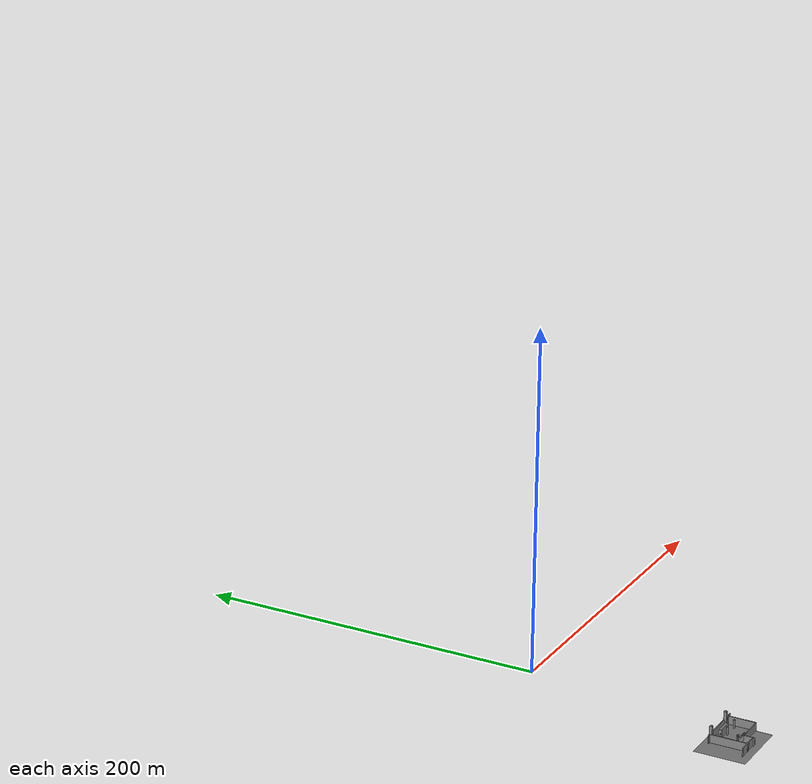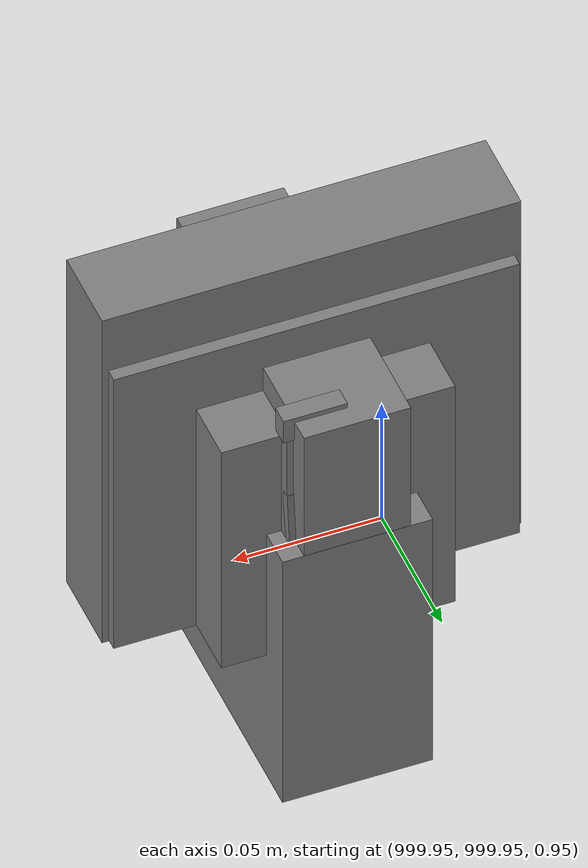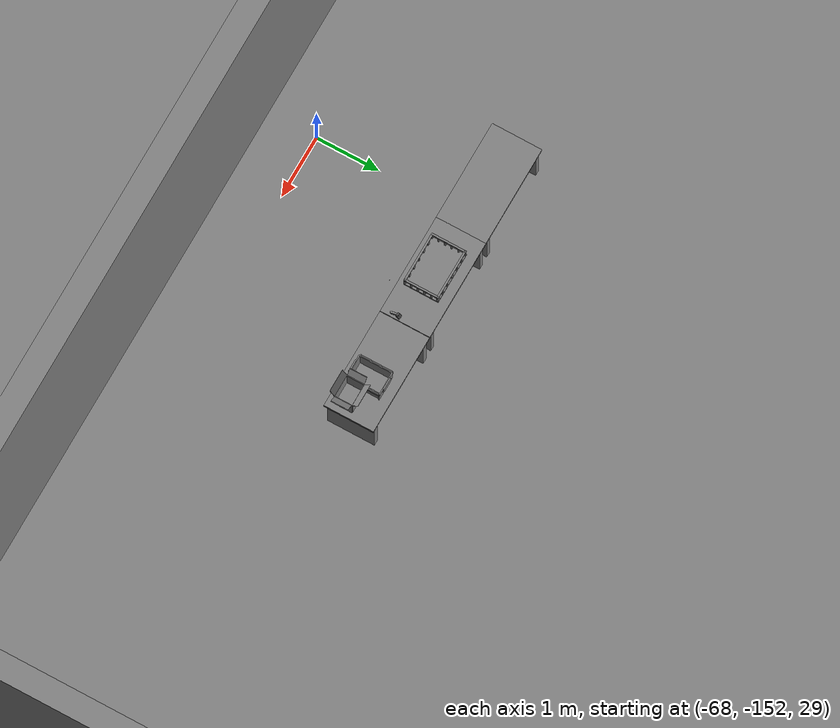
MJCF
<mujoco>
    <option gravity="0.000000000 0.000000000 -9.810000420" timestep="0.0049999999" integrator="implicitfast" density="1.225" viscosity="1.8000001e-05" noslip_iterations="10" iterations="100" sdf_iterations="50">
        <flag multiccd="disable"/>
    </option>
    <size memory="1000M"/>
    <compiler coordinate="local"/>
    <worldbody>
        <light cutoff="30" pos="0 1 1" dir="0 -1 -2"/>
        <light cutoff="30" pos="0 -1 1" dir="0 1 -2"/>
        <body pos="1000.000000000 1000.000000000 1.000000000" euler="0.000000000 0.000000000 180.000000000" name="openloong_gripper_2f85_fix_base_usda_wifi_box">
            <geom contype="1" conaffinity="1" density="1000" type="box" material="" rgba="0.500000000 0.500000000 0.500000000 1.000000000" solimp="0.899999976 0.949999988 0.001000000" friction="1.000000000 0.005000000 0.000100000" solref="0.020000000 1.000000000" margin="0" condim="3" group="0" pos="0.000000000 0.000000000 0.058978677" quat="0.000000000 0.000000047 0.000000000 1.000000000" size="0.068499997 0.018999999 0.059000000" name="openloong_gripper_2f85_fix_base_usda_geom_FEB51D2C_99D6_49EE_AAA1_524D1EA4AB26"/>
            <freejoint name="openloong_gripper_2f85_fix_base_usda_wifi_box_joint"/>
            <site size="0.005000000 0.005000000 0.005000000" rgba="0.500000000 0.500000000 0.500000000 1.000000000" pos="0.000000000 0.000000000 0.000000000" quat="0.999961913 0.008726500 0.000000000 0.000000000" group="0" type="sphere" name="openloong_gripper_2f85_fix_base_usda_wifi_boxsite"/>
        </body>
        <body pos="1000.000000000 1000.000000000 1.000000000" euler="0.000011953 0.000005123 -179.999984741" name="openloong_gripper_2f85_fix_base_usda_intel_box">
            <geom contype="1" conaffinity="1" density="1000" type="box" material="" rgba="0.500000000 0.500000000 0.500000000 1.000000000" solimp="0.899999976 0.949999988 0.001000000" friction="1.000000000 0.005000000 0.000100000" solref="0.020000000 1.000000000" margin="0" condim="3" group="0" pos="0.000000000 -0.000067139 0.000082284" quat="0.707106709 0.000000225 0.000000253 0.707106650" size="0.052800003 0.025300000 0.052800003" name="openloong_gripper_2f85_fix_base_usda_geom_2AF8D811_D31B_475C_A8A1_A8DBD5F0ABDE"/>
            <freejoint name="openloong_gripper_2f85_fix_base_usda_intel_box_joint"/>
            <site size="0.005000000 0.005000000 0.005000000" rgba="0.500000000 0.500000000 0.500000000 1.000000000" pos="0.000000000 0.000000000 0.000000000" quat="0.999961913 0.008726500 0.000000000 0.000000000" group="0" type="sphere" name="openloong_gripper_2f85_fix_base_usda_intel_boxsite"/>
        </body>
        <body pos="-66.112350464 -149.466842651 31.162137985" euler="-168.153442383 -47.751731873 78.787811279" mocap="true" name="spotlight1_SpotLight"/>
        <body pos="1000.000000000 999.999938965 1.000000000" euler="0.000000000 0.000000000 180.000000000" name="openloong_gripper_2f85_fix_base_usda_intelcore_i5">
            <geom contype="1" conaffinity="1" density="1000" type="box" material="" rgba="0.500000000 0.500000000 0.500000000 1.000000000" solimp="0.899999976 0.949999988 0.001000000" friction="1.000000000 0.005000000 0.000100000" solref="0.020000000 1.000000000" margin="0" condim="3" group="0" pos="0.000000000 0.000000000 0.051722717" quat="0.707106709 0.000000000 0.000000000 -0.707106769" size="0.052800000 0.018080002 0.052800000" name="openloong_gripper_2f85_fix_base_usda_geom_82539B14_B1A3_45F5_98D2_C983365B1D82"/>
            <freejoint name="openloong_gripper_2f85_fix_base_usda_intelcore_i5_joint"/>
            <site size="0.005000000 0.005000000 0.005000000" rgba="0.500000000 0.500000000 0.500000000 1.000000000" pos="0.000000000 0.000000000 0.000000000" quat="0.999961913 0.008726534 0.000000000 0.000000000" group="0" type="sphere" name="openloong_gripper_2f85_fix_base_usda_intelcore_i5site"/>
        </body>
        <body pos="1000.000000000 1000.000000000 1.000000000" euler="0.000000000 0.000000000 180.000000000" name="openloong_gripper_2f85_fix_base_usda_cpu_fan">
            <geom contype="1" conaffinity="1" density="1000" type="box" material="" rgba="0.500000000 0.500000000 0.500000000 1.000000000" solimp="0.899999976 0.949999988 0.001000000" friction="1.000000000 0.005000000 0.000100000" solref="0.020000000 1.000000000" margin="0" condim="3" group="0" pos="0.000000000 0.000000000 0.070034981" quat="0.000000000 0.000000000 0.000000000 1.000000000" size="0.070700005 0.014699999 0.070700005" name="openloong_gripper_2f85_fix_base_usda_geom_AB38CF87_E23E_4FF6_8CC5_84DAF609D4E4"/>
            <freejoint name="openloong_gripper_2f85_fix_base_usda_cpu_fan_joint"/>
            <site size="0.005000000 0.005000000 0.005000000" rgba="0.500000000 0.500000000 0.500000000 1.000000000" pos="0.000000000 0.000000000 0.000000000" quat="0.999961913 0.008726535 0.000000000 0.000000000" group="0" type="sphere" name="openloong_gripper_2f85_fix_base_usda_cpu_fancsite"/>
        </body>
        <body pos="-65.984870911 -149.527511597 31.168201447" euler="108.134902954 68.320297241 151.477767944" mocap="true" name="spotlight3_SpotLight"/>
        <body pos="1000.000000000 1000.000000000 1.000000000" euler="0.000000000 0.000000000 180.000000000" name="openloong_gripper_2f85_fix_base_usda_battery_01">
            <geom contype="1" conaffinity="1" density="1000" type="box" material="" rgba="0.500000000 0.500000000 0.500000000 1.000000000" solimp="0.899999976 0.949999988 0.001000000" friction="1.000000000 0.005000000 0.000100000" solref="0.020000000 1.000000000" margin="0" condim="3" group="0" pos="-0.011123657 -0.041940309 0.101691343" quat="1.000000000 0.000000000 0.000000000 0.000000000" size="0.010800000 0.003375000 0.004725000" name="openloong_gripper_2f85_fix_base_usda_geom_1256302D_0159_44DC_AB9C_FDFADD2E248E"/>
            <geom contype="1" conaffinity="1" density="1000" type="box" material="" rgba="0.500000000 0.500000000 0.500000000 1.000000000" solimp="0.899999976 0.949999988 0.001000000" friction="1.000000000 0.005000000 0.000100000" solref="0.020000000 1.000000000" margin="0" condim="3" group="0" pos="-0.010876465 -0.044247437 0.047066893" quat="0.998702705 -0.050920475 0.000000000 0.000000000" size="0.009450001 0.002700000 0.024975000" name="openloong_gripper_2f85_fix_base_usda_geom_1F8EDADC_9E23_4EC2_8281_F1E2F393DBAA"/>
            <geom contype="1" conaffinity="1" density="1000" type="box" material="" rgba="0.500000000 0.500000000 0.500000000 1.000000000" solimp="0.899999976 0.949999988 0.001000000" friction="1.000000000 0.005000000 0.000100000" solref="0.020000000 1.000000000" margin="0" condim="3" group="0" pos="-0.001235962 -0.000659180 0.047381196" quat="1.000000000 0.000000000 0.000000000 0.000000000" size="0.039420001 0.039150000 0.047250003" name="openloong_gripper_2f85_fix_base_usda_geom_8F0702B7_71BE_4D83_B91A_8E24FFD5343B"/>
            <geom contype="1" conaffinity="1" density="1000" type="box" material="" rgba="0.500000000 0.500000000 0.500000000 1.000000000" solimp="0.899999976 0.949999988 0.001000000" friction="1.000000000 0.005000000 0.000100000" solref="0.020000000 1.000000000" margin="0" condim="3" group="0" pos="-0.010876465 -0.039138794 0.009851727" quat="1.000000000 0.000000000 0.000000000 0.000000000" size="0.009450001 0.010800000 0.013500000" name="openloong_gripper_2f85_fix_base_usda_geom_8326A909_9889_4622_9457_AE3707CFD124"/>
            <geom contype="1" conaffinity="1" density="1000" type="box" material="" rgba="0.500000000 0.500000000 0.500000000 1.000000000" solimp="0.899999976 0.949999988 0.001000000" friction="1.000000000 0.005000000 0.000100000" solref="0.020000000 1.000000000" margin="0" condim="3" group="0" pos="-0.010876465 -0.041528322 0.071508206" quat="1.000000000 0.000000000 0.000000000 0.000000000" size="0.009450001 0.002700000 0.027000001" name="openloong_gripper_2f85_fix_base_usda_geom_690E7C12_C1BD_4E9D_83FA_2C9E38786F15"/>
            <freejoint name="openloong_gripper_2f85_fix_base_usda_battery_01_joint"/>
            <site size="0.005000000 0.005000000 0.005000000" rgba="0.500000000 0.500000000 0.500000000 1.000000000" pos="0.000000000 0.000000000 0.000000000" quat="0.999961913 0.008726500 0.000000000 0.000000000" group="0" type="sphere" name="openloong_gripper_2f85_fix_base_usda_battery_01site"/>
        </body>
        <body pos="-66.126762390 -149.214935303 31.167377472" euler="-131.134460449 -38.910758972 -58.184772491" mocap="true" name="spotlight4_SpotLight"/>
        <body pos="-64.866622925 -149.383972168 30.183746338" euler="89.999984741 89.999946594 0.000000000" name="openloong_gripper_2f85_fix_base_usda_bluebox_01">
            <geom contype="1" conaffinity="1" density="1000" type="box" material="" rgba="0.500000000 0.500000000 0.500000000 1.000000000" solimp="0.899999976 0.949999988 0.001000000" friction="1.000000000 0.005000000 0.000100000" solref="0.020000000 1.000000000" margin="0" condim="3" group="0" pos="0.276580811 0.187225342 0.000068665" quat="0.707106948 0.000077471 0.707106352 0.000077486" size="0.100000001 0.057999998 0.010000000" name="openloong_gripper_2f85_fix_base_usda_geom_49358DCC_9EB3_4964_8267_AC1E1CAA176D"/>
            <geom contype="1" conaffinity="1" density="1000" type="box" material="" rgba="0.500000000 0.500000000 0.500000000 1.000000000" solimp="0.899999976 0.949999988 0.001000000" friction="1.000000000 0.005000000 0.000100000" solref="0.020000000 1.000000000" margin="0" condim="3" group="0" pos="0.000000000 0.002883911 0.000000000" quat="0.999999881 0.000000000 0.000000000 0.000000000" size="0.254000008 0.003000000 0.172000006" name="openloong_gripper_2f85_fix_base_usda_geom_F4E0D370_903E_4A73_9EE4_CB85A3D4E9E5"/>
            <geom contype="1" conaffinity="1" density="1000" type="box" material="" rgba="0.500000000 0.500000000 0.500000000 1.000000000" solimp="0.899999976 0.949999988 0.001000000" friction="1.000000000 0.005000000 0.000100000" solref="0.020000000 1.000000000" margin="0" condim="3" group="0" pos="0.000000000 0.124874115 0.173484802" quat="0.999796331 0.020176515 -0.000000015 0.000000030" size="0.259999990 0.119999997 0.007000000" name="openloong_gripper_2f85_fix_base_usda_geom_C3CC578F_5786_41EC_A752_4F1D0A61B5E3"/>
            <geom contype="1" conaffinity="1" density="1000" type="box" material="" rgba="0.500000000 0.500000000 0.500000000 1.000000000" solimp="0.899999976 0.949999988 0.001000000" friction="1.000000000 0.005000000 0.000100000" solref="0.020000000 1.000000000" margin="0" condim="3" group="0" pos="0.000000000 0.124874115 -0.173469543" quat="0.999796331 -0.020176545 -0.000000015 0.000000000" size="0.259999990 0.119999997 0.007000000" name="openloong_gripper_2f85_fix_base_usda_geom_67A61C6C_AB17_4574_9086_ED3501021F78"/>
            <geom contype="1" conaffinity="1" density="1000" type="box" material="" rgba="0.500000000 0.500000000 0.500000000 1.000000000" solimp="0.899999976 0.949999988 0.001000000" friction="1.000000000 0.005000000 0.000100000" solref="0.020000000 1.000000000" margin="0" condim="3" group="0" pos="0.000000000 0.214008331 0.188980103" quat="0.999912977 0.013176724 0.000000015 0.000000000" size="0.259999990 0.029999999 0.012500000" name="openloong_gripper_2f85_fix_base_usda_geom_432A9DCC_FB3E_4C77_95B7_D5EBC0A5B012"/>
            <geom contype="1" conaffinity="1" density="1000" type="box" material="" rgba="0.500000000 0.500000000 0.500000000 1.000000000" solimp="0.899999976 0.949999988 0.001000000" friction="1.000000000 0.005000000 0.000100000" solref="0.020000000 1.000000000" margin="0" condim="3" group="0" pos="-0.258361816 0.125289917 0.001876831" quat="0.702796936 -0.020792112 0.710783124 0.020769298" size="0.189999998 0.119999997 0.009000000" name="openloong_gripper_2f85_fix_base_usda_geom_9AEFF992_2193_4D62_871F_E5122A42D1DB"/>
            <geom contype="1" conaffinity="1" density="1000" type="box" material="" rgba="0.500000000 0.500000000 0.500000000 1.000000000" solimp="0.899999976 0.949999988 0.001000000" friction="1.000000000 0.005000000 0.000100000" solref="0.020000000 1.000000000" margin="0" condim="3" group="0" pos="0.000000000 0.214008331 -0.188980103" quat="0.999912977 -0.013176769 0.000000030 0.000000015" size="0.259999990 0.029999999 0.012500000" name="openloong_gripper_2f85_fix_base_usda_geom_1DAC732D_EB60_42BD_AED1_4E34456060ED"/>
            <geom contype="1" conaffinity="1" density="1000" type="box" material="" rgba="0.500000000 0.500000000 0.500000000 1.000000000" solimp="0.899999976 0.949999988 0.001000000" friction="1.000000000 0.005000000 0.000100000" solref="0.020000000 1.000000000" margin="0" condim="3" group="0" pos="-0.276611328 0.187225342 0.000068665" quat="0.707106650 0.000077441 0.707106709 0.000077456" size="0.100000001 0.057999998 0.010000000" name="openloong_gripper_2f85_fix_base_usda_geom_F8504D99_0589_453C_AE14_3B199A25041B"/>
            <geom contype="1" conaffinity="1" density="1000" type="box" material="" rgba="0.500000000 0.500000000 0.500000000 1.000000000" solimp="0.899999976 0.949999988 0.001000000" friction="1.000000000 0.005000000 0.000100000" solref="0.020000000 1.000000000" margin="0" condim="3" group="0" pos="0.258331299 0.125289917 0.001876831" quat="0.702851415 0.018856421 0.710823774 -0.019329369" size="0.189999998 0.119999997 0.009000000" name="openloong_gripper_2f85_fix_base_usda_geom_327E28EE_180E_4709_9988_B37790C3B854"/>
            <freejoint name="openloong_gripper_2f85_fix_base_usda_bluebox_01_joint"/>
            <site size="0.005000000 0.005000000 0.005000000" rgba="0.500000000 0.500000000 0.500000000 1.000000000" pos="0.000000000 0.000000000 0.000000000" quat="0.999961913 0.008726534 0.000000000 0.000000000" group="0" type="sphere" name="openloong_gripper_2f85_fix_base_usda_bluebox_01site"/>
        </body>
        <body pos="-64.496299744 -149.491867065 30.235729218" euler="0.000000000 0.000000000 89.999946594" name="openloong_gripper_2f85_fix_base_usda_cardboardbox_01">
            <geom contype="1" conaffinity="1" density="1000" type="box" material="" rgba="0.500000000 0.500000000 0.500000000 1.000000000" solimp="0.899999976 0.949999988 0.001000000" friction="1.000000000 0.005000000 0.000100000" solref="0.020000000 1.000000000" margin="0" condim="3" group="0" pos="-0.003166199 -0.004086494 0.005052090" quat="1.000000000 0.000000000 0.000000000 0.000000000" size="0.142499998 0.177500010 0.005000000" name="openloong_gripper_2f85_fix_base_usda_geom_5B388DA8_AA91_4A97_8363_29A305CF5703"/>
            <geom contype="1" conaffinity="1" density="1000" type="box" material="" rgba="0.500000000 0.500000000 0.500000000 1.000000000" solimp="0.899999976 0.949999988 0.001000000" friction="1.000000000 0.005000000 0.000100000" solref="0.020000000 1.000000000" margin="0" condim="3" group="0" pos="-0.003166199 0.170316696 0.150570869" quat="1.000000000 0.000000000 0.000000000 0.000000000" size="0.142499998 0.005000000 0.149999991" name="openloong_gripper_2f85_fix_base_usda_geom_5B378351_B1EB_4288_B021_38863974E1C7"/>
            <geom contype="1" conaffinity="1" density="1000" type="box" material="" rgba="0.500000000 0.500000000 0.500000000 1.000000000" solimp="0.899999976 0.949999988 0.001000000" friction="1.000000000 0.005000000 0.000100000" solref="0.020000000 1.000000000" margin="0" condim="3" group="0" pos="-0.147399902 -0.005307198 0.150570869" quat="1.000000000 0.000000000 0.000000000 0.000000000" size="0.005000000 0.177500010 0.149999991" name="openloong_gripper_2f85_fix_base_usda_geom_02114D48_40B6_407C_93A0_797DF69FB113"/>
            <geom contype="1" conaffinity="1" density="1000" type="box" material="" rgba="0.500000000 0.500000000 0.500000000 1.000000000" solimp="0.899999976 0.949999988 0.001000000" friction="1.000000000 0.005000000 0.000100000" solref="0.020000000 1.000000000" margin="0" condim="3" group="0" pos="0.140275955 -0.005307198 0.150570869" quat="1.000000000 0.000000000 0.000000000 0.000000000" size="0.005000000 0.177500010 0.149999991" name="openloong_gripper_2f85_fix_base_usda_geom_F886E721_DBFC_4B54_82DF_42D2E85470FD"/>
            <geom contype="1" conaffinity="1" density="1000" type="box" material="" rgba="0.500000000 0.500000000 0.500000000 1.000000000" solimp="0.899999976 0.949999988 0.001000000" friction="1.000000000 0.005000000 0.000100000" solref="0.020000000 1.000000000" margin="0" condim="3" group="0" pos="-0.003166199 -0.181550980 0.150570869" quat="1.000000000 0.000000000 0.000000000 0.000000000" size="0.142499998 0.005000000 0.149999991" name="openloong_gripper_2f85_fix_base_usda_geom_A7224007_A5C5_4DED_AC22_066FA33D1746"/>
            <freejoint name="openloong_gripper_2f85_fix_base_usda_cardboardbox_01_joint"/>
            <site size="0.005000000 0.005000000 0.005000000" rgba="0.500000000 0.500000000 0.500000000 1.000000000" pos="0.000000000 0.000000000 0.000000000" quat="0.999961913 0.008726535 0.000000000 0.000000000" group="0" type="sphere" name="openloong_gripper_2f85_fix_base_usda_site_8EF3C2FE_4425_4ECE_842F_1633231FEB94"/>
            <body pos="0.139160156 -0.004048347 0.301930904" euler="-179.999954224 49.383502960 179.999954224" name="openloong_gripper_2f85_fix_base_usda_A1_006">
                <geom contype="1" conaffinity="1" density="1000" type="box" material="" rgba="0.500000000 0.500000000 0.500000000 1.000000000" solimp="0.899999976 0.949999988 0.001000000" friction="1.000000000 0.005000000 0.000100000" solref="0.020000000 1.000000000" margin="0" condim="3" group="0" pos="-0.071587563 0.000009537 0.001745224" quat="0.999999881 0.000000000 0.000000000 0.000000000" size="0.071249999 0.179999992 0.002500000" name="openloong_gripper_2f85_fix_base_usda_geom_ECE00019_A7C0_4177_87DB_DC411B5449AB"/>
                <joint armature="0" stiffness="0.07" damping="0.0099999998" axis="0.000000 1.000000 0.000000" type="hinge" name="openloong_gripper_2f85_fix_base_usda_A1_006"/>
            </body>
            <body pos="-0.145902634 -0.004086494 0.301938057" euler="-180.000000000 -60.000011444 -180.000000000" name="openloong_gripper_2f85_fix_base_usda_A2_006">
                <geom contype="1" conaffinity="1" density="1000" type="box" material="" rgba="0.500000000 0.500000000 0.500000000 1.000000000" solimp="0.899999976 0.949999988 0.001000000" friction="1.000000000 0.005000000 0.000100000" solref="0.020000000 1.000000000" margin="0" condim="3" group="0" pos="0.071268082 0.000009537 0.002717972" quat="0.000002921 0.000000000 -0.000000030 0.999999881" size="0.071249999 0.179999992 0.002500000" name="openloong_gripper_2f85_fix_base_usda_geom_406FD711_1D37_4EC1_AF1B_D9F42E36BB93"/>
                <joint armature="0" stiffness="0.07" damping="0.0099999998" axis="0.000000 1.000000 0.000000" type="hinge" name="openloong_gripper_2f85_fix_base_usda_A2_006"/>
            </body>
            <body pos="-0.003385544 0.175991058 0.301930904" euler="-125.858116150 -0.000004561 0.000002331" name="openloong_gripper_2f85_fix_base_usda_B2_006">
                <geom contype="1" conaffinity="1" density="1000" type="box" material="" rgba="0.500000000 0.500000000 0.500000000 1.000000000" solimp="0.899999976 0.949999988 0.001000000" friction="1.000000000 0.005000000 0.000100000" solref="0.020000000 1.000000000" margin="0" condim="3" group="0" pos="0.000009537 -0.070939064 -0.002470016" quat="0.999614120 0.027776197 -0.000000015 0.000000030" size="0.137500003 0.064999998 0.005000000" name="openloong_gripper_2f85_fix_base_usda_geom_9EF8CD62_39E8_481F_BC9B_A7BAACE98741"/>
                <joint armature="0" stiffness="0.07" damping="0.0099999998" axis="1.000000 0.000000 0.000000" type="hinge" name="openloong_gripper_2f85_fix_base_usda_B2_006"/>
            </body>
            <body pos="-0.003385544 -0.184140205 0.301938057" euler="147.805557251 0.000000000 0.000000000" name="openloong_gripper_2f85_fix_base_usda_B1_006">
                <geom contype="1" conaffinity="1" density="1000" type="box" material="" rgba="0.500000000 0.500000000 0.500000000 1.000000000" solimp="0.899999976 0.949999988 0.001000000" friction="1.000000000 0.005000000 0.000100000" solref="0.020000000 1.000000000" margin="0" condim="3" group="0" pos="-0.000028610 0.070202351 -0.002703667" quat="0.999614179 -0.027776167 0.000000000 0.000000000" size="0.137500003 0.064999998 0.005000000" name="openloong_gripper_2f85_fix_base_usda_geom_DF832627_9FB4_4159_A2E6_54F06BC8B40C"/>
                <joint armature="0" stiffness="0.07" damping="0.0099999998" axis="1.000000 0.000000 0.000000" type="hinge" name="openloong_gripper_2f85_fix_base_usda_B1_006"/>
            </body>
        </body>
        <body pos="-65.882858276 -149.481979370 30.229999542" euler="-64.487716675 0.000000000 0.000000000" name="openloong_gripper_2f85_fix_base_usda_Barcode">
            <geom contype="1" conaffinity="1" density="1000" type="box" material="" rgba="0.500000000 0.500000000 0.500000000 1.000000000" solimp="0.899999976 0.949999988 0.001000000" friction="1.000000000 0.005000000 0.000100000" solref="0.020000000 1.000000000" margin="0" condim="3" group="0" pos="0.000000000 0.013038635 0.001419067" quat="0.000000000 0.000000000 0.000000000 1.000000119" size="0.034000002 0.010000000 0.017999999" name="openloong_gripper_2f85_fix_base_usda_geom_E3C400EF_3E6F_4ACF_BA1B_7632FB56C26E"/>
            <geom contype="1" conaffinity="1" density="1000" type="box" material="" rgba="0.500000000 0.500000000 0.500000000 1.000000000" solimp="0.899999976 0.949999988 0.001000000" friction="1.000000000 0.005000000 0.000100000" solref="0.020000000 1.000000000" margin="0" condim="3" group="0" pos="0.000000000 -0.035301208 -0.007095337" quat="0.000000000 0.000000000 -0.043619365 0.999048233" size="0.028999999 0.010000000 0.020000000" name="openloong_gripper_2f85_fix_base_usda_geom_66641CD1_5A7C_4018_AB4E_EC57DAEA5AF5"/>
            <geom contype="1" conaffinity="1" density="1000" type="box" material="" rgba="0.500000000 0.500000000 0.500000000 1.000000000" solimp="0.899999976 0.949999988 0.001000000" friction="1.000000000 0.005000000 0.000100000" solref="0.020000000 1.000000000" margin="0" condim="3" group="0" pos="0.000000000 -0.043411255 -0.011749268" quat="0.922262907 0.386563420 0.000000000 0.000000000" size="0.026000001 0.010000000 0.020000000" name="openloong_gripper_2f85_fix_base_usda_geom_12B65DA2_E86D_4793_ADE2_376BEC41EB65"/>
            <geom contype="1" conaffinity="1" density="1000" type="box" material="" rgba="0.500000000 0.500000000 0.500000000 1.000000000" solimp="0.899999976 0.949999988 0.001000000" friction="1.000000000 0.005000000 0.000100000" solref="0.020000000 1.000000000" margin="0" condim="3" group="0" pos="0.000000000 -0.016967773 -0.031860352" quat="0.000000000 0.000000000 0.000000000 1.000000119" size="0.008000000 0.010000000 0.013000000" name="openloong_gripper_2f85_fix_base_usda_geom_A1347B25_4C7D_4449_84EC_5C104BF54A08"/>
            <geom contype="1" conaffinity="1" density="1000" type="box" material="" rgba="0.500000000 0.500000000 0.500000000 1.000000000" solimp="0.899999976 0.949999988 0.001000000" friction="1.000000000 0.005000000 0.000100000" solref="0.020000000 1.000000000" margin="0" condim="3" group="0" pos="0.000000000 -0.001869202 0.000312805" quat="0.953716993 0.300705761 0.000000000 0.000000000" size="0.032000002 0.010000000 0.018999999" name="openloong_gripper_2f85_fix_base_usda_geom_E0413A85_0480_434A_B128_5665ED323C15"/>
            <geom contype="1" conaffinity="1" density="1000" type="box" material="" rgba="0.500000000 0.500000000 0.500000000 1.000000000" solimp="0.899999976 0.949999988 0.001000000" friction="1.000000000 0.005000000 0.000100000" solref="0.020000000 1.000000000" margin="0" condim="3" group="0" pos="0.000000000 -0.019531250 -0.003173828" quat="0.953716993 0.300705761 0.000000000 0.000000000" size="0.030999999 0.010000000 0.020000000" name="openloong_gripper_2f85_fix_base_usda_geom_04E2A704_2B89_4142_909F_AE83D523BAC9"/>
            <geom contype="1" conaffinity="1" density="1000" type="box" material="" rgba="0.500000000 0.500000000 0.500000000 1.000000000" solimp="0.899999976 0.949999988 0.001000000" friction="1.000000000 0.005000000 0.000100000" solref="0.020000000 1.000000000" margin="0" condim="3" group="0" pos="0.000000000 -0.035301208 -0.007095337" quat="0.953716993 0.300705761 0.000000000 0.000000000" size="0.028999999 0.010000000 0.020000000" name="openloong_gripper_2f85_fix_base_usda_geom_3B3867D5_ED32_483D_BE92_8E41D9839C96"/>
            <geom contype="1" conaffinity="1" density="1000" type="box" material="" rgba="0.500000000 0.500000000 0.500000000 1.000000000" solimp="0.899999976 0.949999988 0.001000000" friction="1.000000000 0.005000000 0.000100000" solref="0.020000000 1.000000000" margin="0" condim="3" group="0" pos="0.000000000 -0.042617798 -0.071121216" quat="0.000000000 0.000000000 0.000000000 1.000000119" size="0.013000000 0.021000000 0.059999999" name="openloong_gripper_2f85_fix_base_usda_geom_C5061902_7F1E_403D_B12C_2CE9AE0F38F5"/>
            <freejoint name="openloong_gripper_2f85_fix_base_usda_Barcode_joint"/>
            <site size="0.005000000 0.005000000 0.005000000" rgba="0.500000000 0.500000000 0.500000000 1.000000000" pos="0.000000000 0.000000000 0.000000000" quat="1.000000000 0.000000000 0.000000000 0.000000000" group="0" type="sphere" name="openloong_gripper_2f85_fix_base_usda_Barcode_site"/>
        </body>
        <body pos="-66.745018005 -149.392349243 30.184000015" euler="0.000000000 0.000000000 89.999946594" name="[22332930110468]_Basket_01">
            <geom contype="1" conaffinity="1" density="1000" type="box" material="" rgba="0.500000000 0.500000000 0.500000000 1.000000000" solimp="0.899999976 0.949999988 0.001000000" friction="1.000000000 0.005000000 0.000100000" solref="0.020000000 1.000000000" margin="0" condim="3" group="0" pos="-0.052425385 0.389207840 0.089787483" quat="0.707107008 0.000000000 0.000000000 0.707106411" size="0.014249999 0.014249999 0.059999999" name="[22332930110468]_geom_F3E873B1_49E8_4E6A_9B05_4E96E6E4624D"/>
            <geom contype="1" conaffinity="1" density="1000" type="box" material="" rgba="0.500000000 0.500000000 0.500000000 1.000000000" solimp="0.899999976 0.949999988 0.001000000" friction="1.000000000 0.005000000 0.000100000" solref="0.020000000 1.000000000" margin="0" condim="3" group="0" pos="0.264015198 -0.133043289 0.089787483" quat="0.707107008 0.000000000 0.000000000 0.707106411" size="0.014249999 0.014249999 0.059999999" name="[22332930110468]_geom_10BFB7C3_215A_4EAF_B498_E3445A667AA8"/>
            <geom contype="1" conaffinity="1" density="1000" type="box" material="" rgba="0.500000000 0.500000000 0.500000000 1.000000000" solimp="0.899999976 0.949999988 0.001000000" friction="1.000000000 0.005000000 0.000100000" solref="0.020000000 1.000000000" margin="0" condim="3" group="0" pos="-0.264015198 -0.265548706 0.089793205" quat="0.707107008 0.000000000 0.000000000 0.707106411" size="0.014249999 0.014249999 0.059999999" name="[22332930110468]_geom_82288302_0D38_45DF_87B3_8600A4FB96C0"/>
            <geom contype="1" conaffinity="1" density="1000" type="box" material="" rgba="0.500000000 0.500000000 0.500000000 1.000000000" solimp="0.899999976 0.949999988 0.001000000" friction="1.000000000 0.005000000 0.000100000" solref="0.020000000 1.000000000" margin="0" condim="3" group="0" pos="-0.160263062 -0.389322281 0.089793205" quat="0.707107008 0.000000000 0.000000000 0.707106411" size="0.014249999 0.014249999 0.059999999" name="[22332930110468]_geom_D99D5F3D_A169_4220_8B97_77DE4B431DC1"/>
            <geom contype="1" conaffinity="1" density="1000" type="box" material="" rgba="0.500000000 0.500000000 0.500000000 1.000000000" solimp="0.899999976 0.949999988 0.001000000" friction="1.000000000 0.005000000 0.000100000" solref="0.020000000 1.000000000" margin="0" condim="3" group="0" pos="0.162265778 -0.389322281 0.089787483" quat="0.707107008 0.000000000 0.000000000 0.707106411" size="0.014249999 0.014249999 0.059999999" name="[22332930110468]_geom_5DB52C69_7704_4805_8698_68582DB07E4C"/>
            <geom contype="1" conaffinity="1" density="1000" type="box" material="" rgba="0.500000000 0.500000000 0.500000000 1.000000000" solimp="0.899999976 0.949999988 0.001000000" friction="1.000000000 0.005000000 0.000100000" solref="0.020000000 1.000000000" margin="0" condim="3" group="0" pos="0.264015198 0.389207840 0.089787483" quat="0.707107008 0.000000000 0.000000000 0.707106411" size="0.014249999 0.014249999 0.059999999" name="[22332930110468]_geom_73EF2E1E_6F9E_4C7F_97E0_A2FC1DF0878A"/>
            <geom contype="1" conaffinity="1" density="1000" type="box" material="" rgba="0.500000000 0.500000000 0.500000000 1.000000000" solimp="0.899999976 0.949999988 0.001000000" friction="1.000000000 0.005000000 0.000100000" solref="0.020000000 1.000000000" margin="0" condim="3" group="0" pos="-0.264015198 -0.133043289 0.089793205" quat="0.707107008 0.000000000 0.000000000 0.707106411" size="0.014249999 0.014249999 0.059999999" name="[22332930110468]_geom_A3378121_4E6E_4116_B2E1_D1299606FB61"/>
            <geom contype="1" conaffinity="1" density="1000" type="box" material="" rgba="0.500000000 0.500000000 0.500000000 1.000000000" solimp="0.899999976 0.949999988 0.001000000" friction="1.000000000 0.005000000 0.000100000" solref="0.020000000 1.000000000" margin="0" condim="3" group="0" pos="-0.264026642 0.269256592 0.089793205" quat="0.707107008 0.000000000 0.000000000 0.707106411" size="0.014249999 0.014249999 0.059999999" name="[22332930110468]_geom_95A12E45_B04E_4809_8512_37E6836E6DE2"/>
            <geom contype="1" conaffinity="1" density="1000" type="box" material="" rgba="0.500000000 0.500000000 0.500000000 1.000000000" solimp="0.899999976 0.949999988 0.001000000" friction="1.000000000 0.005000000 0.000100000" solref="0.020000000 1.000000000" margin="0" condim="3" group="0" pos="0.054462433 0.389207840 0.089787483" quat="0.707107008 0.000000000 0.000000000 0.707106411" size="0.014249999 0.014249999 0.059999999" name="[22332930110468]_geom_D80FED52_B21D_4289_8648_E0DB8F99A0DB"/>
            <geom contype="1" conaffinity="1" density="1000" type="box" material="" rgba="0.500000000 0.500000000 0.500000000 1.000000000" solimp="0.899999976 0.949999988 0.001000000" friction="1.000000000 0.005000000 0.000100000" solref="0.020000000 1.000000000" margin="0" condim="3" group="0" pos="0.054462433 -0.389322281 0.089787483" quat="0.707107008 0.000000000 0.000000000 0.707106411" size="0.014249999 0.014249999 0.059999999" name="[22332930110468]_geom_D4FFED2F_86E3_46BB_B454_80F008B859D3"/>
            <geom contype="1" conaffinity="1" density="1000" type="box" material="" rgba="0.500000000 0.500000000 0.500000000 1.000000000" solimp="0.899999976 0.949999988 0.001000000" friction="1.000000000 0.005000000 0.000100000" solref="0.020000000 1.000000000" margin="0" condim="3" group="0" pos="0.264015198 0.269256592 0.089793205" quat="0.707107008 0.000000000 0.000000000 0.707106411" size="0.014249999 0.014249999 0.059999999" name="[22332930110468]_geom_CBAFE14D_43F1_40D8_9116_2FA105769B0F"/>
            <geom contype="1" conaffinity="1" density="1000" type="box" material="" rgba="0.500000000 0.500000000 0.500000000 1.000000000" solimp="0.899999976 0.949999988 0.001000000" friction="1.000000000 0.005000000 0.000100000" solref="0.020000000 1.000000000" margin="0" condim="3" group="0" pos="0.264015198 -0.389322281 0.089787483" quat="0.707107008 0.000000000 0.000000000 0.707106411" size="0.014249999 0.014249999 0.059999999" name="[22332930110468]_geom_1642F501_18A7_4529_AEAD_A540BD7B5E78"/>
            <geom contype="1" conaffinity="1" density="1000" type="box" material="" rgba="0.500000000 0.500000000 0.500000000 1.000000000" solimp="0.899999976 0.949999988 0.001000000" friction="1.000000000 0.005000000 0.000100000" solref="0.020000000 1.000000000" margin="0" condim="3" group="0" pos="0.000000000 0.000000000 0.015998840" quat="0.707107008 0.000000000 0.000000000 0.707106411" size="0.403499991 0.279000014 0.015750000" name="[22332930110468]_geom_03B52398_8555_4500_888B_8E0014C5278D"/>
            <geom contype="1" conaffinity="1" density="1000" type="box" material="" rgba="0.500000000 0.500000000 0.500000000 1.000000000" solimp="0.899999976 0.949999988 0.001000000" friction="1.000000000 0.005000000 0.000100000" solref="0.020000000 1.000000000" margin="0" condim="3" group="0" pos="0.000000000 -0.389476776 0.163619041" quat="0.707107008 0.000000000 0.000000000 0.707106411" size="0.015000000 0.277500004 0.015750000" name="[22332930110468]_geom_9A9D90EC_A908_437A_8290_D8529516CC80"/>
            <geom contype="1" conaffinity="1" density="1000" type="box" material="" rgba="0.500000000 0.500000000 0.500000000 1.000000000" solimp="0.899999976 0.949999988 0.001000000" friction="1.000000000 0.005000000 0.000100000" solref="0.020000000 1.000000000" margin="0" condim="3" group="0" pos="0.162265778 0.389207840 0.089787483" quat="0.707107008 0.000000000 0.000000000 0.707106411" size="0.014249999 0.014249999 0.059999999" name="[22332930110468]_geom_22E6EA64_A032_42EA_B673_517815CBAFA6"/>
            <geom contype="1" conaffinity="1" density="1000" type="box" material="" rgba="0.500000000 0.500000000 0.500000000 1.000000000" solimp="0.899999976 0.949999988 0.001000000" friction="1.000000000 0.005000000 0.000100000" solref="0.020000000 1.000000000" margin="0" condim="3" group="0" pos="0.000000000 0.389471054 0.163619041" quat="0.707107008 0.000000000 0.000000000 0.707106411" size="0.015000000 0.277500004 0.015750000" name="[22332930110468]_geom_7C88D3D3_300E_4B67_8E4B_D0F70470FCBB"/>
            <geom contype="1" conaffinity="1" density="1000" type="box" material="" rgba="0.500000000 0.500000000 0.500000000 1.000000000" solimp="0.899999976 0.949999988 0.001000000" friction="1.000000000 0.005000000 0.000100000" solref="0.020000000 1.000000000" margin="0" condim="3" group="0" pos="-0.263511658 0.000000000 0.163619041" quat="0.707107008 0.000000000 0.000000000 0.707106411" size="0.403499991 0.015000000 0.015750000" name="[22332930110468]_geom_89915A01_BB6D_41D3_AAAD_882B4A335245"/>
            <geom contype="1" conaffinity="1" density="1000" type="box" material="" rgba="0.500000000 0.500000000 0.500000000 1.000000000" solimp="0.899999976 0.949999988 0.001000000" friction="1.000000000 0.005000000 0.000100000" solref="0.020000000 1.000000000" margin="0" condim="3" group="0" pos="-0.264015198 0.141334534 0.089793205" quat="0.707107008 0.000000000 0.000000000 0.707106411" size="0.014249999 0.014249999 0.059999999" name="[22332930110468]_geom_D0AF77F1_A4AC_4DDA_B00D_4A99048AFCA6"/>
            <geom contype="1" conaffinity="1" density="1000" type="box" material="" rgba="0.500000000 0.500000000 0.500000000 1.000000000" solimp="0.899999976 0.949999988 0.001000000" friction="1.000000000 0.005000000 0.000100000" solref="0.020000000 1.000000000" margin="0" condim="3" group="0" pos="0.264015198 -0.265548706 0.089787483" quat="0.707107008 0.000000000 0.000000000 0.707106411" size="0.014249999 0.014249999 0.059999999" name="[22332930110468]_geom_4911317E_0B94_462E_97BC_117039986B3B"/>
            <geom contype="1" conaffinity="1" density="1000" type="box" material="" rgba="0.500000000 0.500000000 0.500000000 1.000000000" solimp="0.899999976 0.949999988 0.001000000" friction="1.000000000 0.005000000 0.000100000" solref="0.020000000 1.000000000" margin="0" condim="3" group="0" pos="-0.160263062 0.389207840 0.089787483" quat="0.707107008 0.000000000 0.000000000 0.707106411" size="0.014249999 0.014249999 0.059999999" name="[22332930110468]_geom_E3C757F9_F29F_4FB5_8A3F_C2928EAF6477"/>
            <geom contype="1" conaffinity="1" density="1000" type="box" material="" rgba="0.500000000 0.500000000 0.500000000 1.000000000" solimp="0.899999976 0.949999988 0.001000000" friction="1.000000000 0.005000000 0.000100000" solref="0.020000000 1.000000000" margin="0" condim="3" group="0" pos="-0.052425385 -0.389322281 0.089787483" quat="0.707107008 0.000000000 0.000000000 0.707106411" size="0.014249999 0.014249999 0.059999999" name="[22332930110468]_geom_0A7F04C9_565F_4D53_A1E9_E6B424669E23"/>
            <geom contype="1" conaffinity="1" density="1000" type="box" material="" rgba="0.500000000 0.500000000 0.500000000 1.000000000" solimp="0.899999976 0.949999988 0.001000000" friction="1.000000000 0.005000000 0.000100000" solref="0.020000000 1.000000000" margin="0" condim="3" group="0" pos="-0.264026642 -0.389322281 0.089793205" quat="0.707107008 0.000000000 0.000000000 0.707106411" size="0.014249999 0.014249999 0.059999999" name="[22332930110468]_geom_5FE324C3_EFDF_4AA3_BBE8_B551DA7B038C"/>
            <geom contype="1" conaffinity="1" density="1000" type="box" material="" rgba="0.500000000 0.500000000 0.500000000 1.000000000" solimp="0.899999976 0.949999988 0.001000000" friction="1.000000000 0.005000000 0.000100000" solref="0.020000000 1.000000000" margin="0" condim="3" group="0" pos="0.264015198 0.141334534 0.089787483" quat="0.707107008 0.000000000 0.000000000 0.707106411" size="0.014249999 0.014249999 0.059999999" name="[22332930110468]_geom_610615C7_0793_4BFD_A1EC_05A6A16C0F76"/>
            <geom contype="1" conaffinity="1" density="1000" type="box" material="" rgba="0.500000000 0.500000000 0.500000000 1.000000000" solimp="0.899999976 0.949999988 0.001000000" friction="1.000000000 0.005000000 0.000100000" solref="0.020000000 1.000000000" margin="0" condim="3" group="0" pos="-0.264015198 0.389207840 0.089793205" quat="0.707107008 0.000000000 0.000000000 0.707106411" size="0.014249999 0.014249999 0.059999999" name="[22332930110468]_geom_8E5D839C_D445_4672_915C_5942E905DD61"/>
            <geom contype="1" conaffinity="1" density="1000" type="box" material="" rgba="0.500000000 0.500000000 0.500000000 1.000000000" solimp="0.899999976 0.949999988 0.001000000" friction="1.000000000 0.005000000 0.000100000" solref="0.020000000 1.000000000" margin="0" condim="3" group="0" pos="0.264015198 0.004480362 0.089787483" quat="0.707107008 0.000000000 0.000000000 0.707106411" size="0.014249999 0.014249999 0.059999999" name="[22332930110468]_geom_044D37F2_D5DF_4D4D_BEBF_D2CD5D292172"/>
            <geom contype="1" conaffinity="1" density="1000" type="box" material="" rgba="0.500000000 0.500000000 0.500000000 1.000000000" solimp="0.899999976 0.949999988 0.001000000" friction="1.000000000 0.005000000 0.000100000" solref="0.020000000 1.000000000" margin="0" condim="3" group="0" pos="0.263694763 -0.000011444 0.163619041" quat="0.707107008 0.000000000 0.000000000 0.707106411" size="0.403499991 0.015000000 0.015750000" name="[22332930110468]_geom_03741A49_A3AE_444A_AD3A_FF4988A0C0D1"/>
            <geom contype="1" conaffinity="1" density="1000" type="box" material="" rgba="0.500000000 0.500000000 0.500000000 1.000000000" solimp="0.899999976 0.949999988 0.001000000" friction="1.000000000 0.005000000 0.000100000" solref="0.020000000 1.000000000" margin="0" condim="3" group="0" pos="-0.264015198 0.004480362 0.089793205" quat="0.707107008 0.000000000 0.000000000 0.707106411" size="0.014249999 0.014249999 0.059999999" name="[22332930110468]_geom_4D48B027_0FF9_4DA3_95F5_E9383DF7512E"/>
            <freejoint name="[22332930110468]_joint_DDC2AF56_4FFE_47A3_BC4D_2D70F98BAACE"/>
        </body>
        <body pos="0.000000000 0.000000000 0.000000000" euler="0.000000000 0.000000000 0.000000000" name="Static Objects_Static Objects">
            <geom contype="1" conaffinity="1" density="1000" type="box" material="" rgba="0.500000000 0.500000000 0.500000000 1.000000000" solimp="0.899999976 0.949999988 0.001000000" friction="1.000000000 0.005000000 0.000100000" solref="0.020000000 1.000000000" margin="0" condim="3" group="0" pos="-67.544113159 -149.365814209 29.727830887" quat="0.500000417 0.499999970 0.499999553 0.499999970" size="0.381000012 0.319999993 0.041000001" name="Static Objects_geom_120E64A6_DD8B_4DF2_990C_1C9DA09A4927"/>
            <geom contype="1" conaffinity="1" density="1000" type="box" material="" rgba="0.500000000 0.500000000 0.500000000 1.000000000" solimp="0.899999976 0.949999988 0.001000000" friction="1.000000000 0.005000000 0.000100000" solref="0.020000000 1.000000000" margin="0" condim="3" group="0" pos="-68.239501953 -149.365814209 30.086868286" quat="0.500000417 0.499999970 0.499999553 0.499999970" size="0.370999992 0.039500002 0.745000005" name="Static Objects_geom_406BE809_1B5F_40C2_B4DA_949DB5AA04DC"/>
            <geom contype="1" conaffinity="1" density="1000" type="box" material="" rgba="0.500000000 0.500000000 0.500000000 1.000000000" solimp="0.899999976 0.949999988 0.001000000" friction="1.000000000 0.005000000 0.000100000" solref="0.020000000 1.000000000" margin="0" condim="3" group="0" pos="-68.239501953 -149.365814209 30.147235870" quat="0.500000417 0.499999970 0.499999553 0.499999970" size="0.400000006 0.022000000 0.800000012" name="Static Objects_geom_6D611AA4_AF5F_43B2_9B7C_7EDB5B356DF5"/>
            <geom contype="1" conaffinity="1" density="1000" type="box" material="" rgba="0.500000000 0.500000000 0.500000000 1.000000000" solimp="0.899999976 0.949999988 0.001000000" friction="1.000000000 0.005000000 0.000100000" solref="0.020000000 1.000000000" margin="0" condim="3" group="0" pos="-68.934890747 -149.365814209 29.727830887" quat="0.500000417 0.499999970 0.499999553 0.499999970" size="0.381000012 0.319999993 0.041000001" name="Static Objects_geom_E6DA570D_23BA_4B5D_B8D3_4A5379BBA440"/>
            <geom contype="1" conaffinity="1" density="1000" type="box" material="" rgba="0.500000000 0.500000000 0.500000000 1.000000000" solimp="0.899999976 0.949999988 0.001000000" friction="1.000000000 0.005000000 0.000100000" solref="0.020000000 1.000000000" margin="0" condim="3" group="0" pos="-68.239501953 -149.365814209 29.561563492" quat="0.500000417 0.499999970 0.499999553 0.499999970" size="0.020000000 0.022000000 0.660000026" name="Static Objects_geom_44DB74B8_F41C_4BC2_9806_CD486472A08E"/>
            <geom contype="1" conaffinity="1" density="1000" type="box" material="" rgba="0.500000000 0.500000000 0.500000000 1.000000000" solimp="0.899999976 0.949999988 0.001000000" friction="1.000000000 0.005000000 0.000100000" solref="0.020000000 1.000000000" margin="0" condim="3" group="0" pos="-65.945671082 -149.365814209 29.727830887" quat="0.500000417 0.499999970 0.499999553 0.499999970" size="0.381000012 0.319999993 0.041000001" name="Static Objects_geom_A2FE3564_9259_4AA9_B57C_E42CAEEF0564"/>
            <geom contype="1" conaffinity="1" density="1000" type="box" material="" rgba="0.500000000 0.500000000 0.500000000 1.000000000" solimp="0.899999976 0.949999988 0.001000000" friction="1.000000000 0.005000000 0.000100000" solref="0.020000000 1.000000000" margin="0" condim="3" group="0" pos="-66.641059875 -149.365814209 30.086868286" quat="0.500000417 0.499999970 0.499999553 0.499999970" size="0.370999992 0.039500002 0.745000005" name="Static Objects_geom_FED1DE26_F31C_4320_BC73_48FB4519974E"/>
            <geom contype="1" conaffinity="1" density="1000" type="box" material="" rgba="0.500000000 0.500000000 0.500000000 1.000000000" solimp="0.899999976 0.949999988 0.001000000" friction="1.000000000 0.005000000 0.000100000" solref="0.020000000 1.000000000" margin="0" condim="3" group="0" pos="-66.641059875 -149.365814209 30.147235870" quat="0.500000417 0.499999970 0.499999553 0.499999970" size="0.400000006 0.022000000 0.800000012" name="Static Objects_geom_6AD810D9_81BF_4A68_A44D_153A4A45F8AE"/>
            <geom contype="1" conaffinity="1" density="1000" type="box" material="" rgba="0.500000000 0.500000000 0.500000000 1.000000000" solimp="0.899999976 0.949999988 0.001000000" friction="1.000000000 0.005000000 0.000100000" solref="0.020000000 1.000000000" margin="0" condim="3" group="0" pos="-67.336448669 -149.365814209 29.727830887" quat="0.500000417 0.499999970 0.499999553 0.499999970" size="0.381000012 0.319999993 0.041000001" name="Static Objects_geom_10792D17_AB16_4EF2_811C_E096C4CDE071"/>
            <geom contype="1" conaffinity="1" density="1000" type="box" material="" rgba="0.500000000 0.500000000 0.500000000 1.000000000" solimp="0.899999976 0.949999988 0.001000000" friction="1.000000000 0.005000000 0.000100000" solref="0.020000000 1.000000000" margin="0" condim="3" group="0" pos="-66.641059875 -149.365814209 29.561563492" quat="0.500000417 0.499999970 0.499999553 0.499999970" size="0.020000000 0.022000000 0.660000026" name="Static Objects_geom_FE0DDBBE_6A7C_405E_8DCA_E2795AAB0DBD"/>
            <geom contype="1" conaffinity="1" density="1000" type="box" material="" rgba="0.500000000 0.500000000 0.500000000 1.000000000" solimp="0.899999976 0.949999988 0.001000000" friction="1.000000000 0.005000000 0.000100000" solref="0.020000000 1.000000000" margin="0" condim="3" group="0" pos="-64.338577271 -149.365814209 29.727830887" quat="0.500000417 0.499999970 0.499999553 0.499999970" size="0.381000012 0.319999993 0.041000001" name="Static Objects_geom_F5E19037_0BA9_4E63_BCAE_D4EE60B54B1A"/>
            <geom contype="1" conaffinity="1" density="1000" type="box" material="" rgba="0.500000000 0.500000000 0.500000000 1.000000000" solimp="0.899999976 0.949999988 0.001000000" friction="1.000000000 0.005000000 0.000100000" solref="0.020000000 1.000000000" margin="0" condim="3" group="0" pos="-65.033966064 -149.365814209 30.086868286" quat="0.500000417 0.499999970 0.499999553 0.499999970" size="0.370999992 0.039500002 0.745000005" name="Static Objects_geom_CF222D85_1C76_4127_B3A6_6C0C25F6E7F0"/>
            <geom contype="1" conaffinity="1" density="1000" type="box" material="" rgba="0.500000000 0.500000000 0.500000000 1.000000000" solimp="0.899999976 0.949999988 0.001000000" friction="1.000000000 0.005000000 0.000100000" solref="0.020000000 1.000000000" margin="0" condim="3" group="0" pos="-65.033966064 -149.365814209 30.147235870" quat="0.500000417 0.499999970 0.499999553 0.499999970" size="0.400000006 0.022000000 0.800000012" name="Static Objects_geom_281B28BB_D939_4A13_A6D5_2BAE7D01B990"/>
            <geom contype="1" conaffinity="1" density="1000" type="box" material="" rgba="0.500000000 0.500000000 0.500000000 1.000000000" solimp="0.899999976 0.949999988 0.001000000" friction="1.000000000 0.005000000 0.000100000" solref="0.020000000 1.000000000" margin="0" condim="3" group="0" pos="-65.729354858 -149.365814209 29.727830887" quat="0.500000417 0.499999970 0.499999553 0.499999970" size="0.381000012 0.319999993 0.041000001" name="Static Objects_geom_D566CD84_E8B3_4E44_8D9C_30F80BB4AC96"/>
            <geom contype="1" conaffinity="1" density="1000" type="box" material="" rgba="0.500000000 0.500000000 0.500000000 1.000000000" solimp="0.899999976 0.949999988 0.001000000" friction="1.000000000 0.005000000 0.000100000" solref="0.020000000 1.000000000" margin="0" condim="3" group="0" pos="-65.033966064 -149.365814209 29.561563492" quat="0.500000417 0.499999970 0.499999553 0.499999970" size="0.020000000 0.022000000 0.660000026" name="Static Objects_geom_54783145_6D82_4E63_8BC1_8E22EB644FEC"/>
            <geom contype="1" conaffinity="1" density="1000" type="box" material="" rgba="0.500000000 0.500000000 0.500000000 1.000000000" solimp="0.899999976 0.949999988 0.001000000" friction="1.000000000 0.005000000 0.000100000" solref="0.020000000 1.000000000" margin="0" condim="3" group="0" pos="-61.754566193 -137.853729248 33.906845093" quat="0.707107067 0.000000000 0.000000000 0.707106471" size="0.759999990 0.759999990 4.500000000" name="Static Objects_geom_5CA449B3_665A_40F4_A617_DE295E7F3848"/>
            <geom contype="1" conaffinity="1" density="1000" type="box" material="" rgba="0.500000000 0.500000000 0.500000000 1.000000000" solimp="0.899999976 0.949999988 0.001000000" friction="1.000000000 0.005000000 0.000100000" solref="0.020000000 1.000000000" margin="0" condim="3" group="0" pos="-57.511135101 -144.927108765 31.707921982" quat="1.000000000 0.000000000 0.000000000 0.000000000" size="0.200000003 8.000000000 2.299999952" name="Static Objects_geom_12C04079_E267_49B8_8D1B_10C2585A9D6C"/>
            <geom contype="1" conaffinity="1" density="1000" type="box" material="" rgba="0.500000000 0.500000000 0.500000000 1.000000000" solimp="0.899999976 0.949999988 0.001000000" friction="1.000000000 0.005000000 0.000100000" solref="0.020000000 1.000000000" margin="0" condim="3" group="0" pos="-80.517646790 -157.574050903 31.688196182" quat="0.707107067 0.000000000 0.000000000 0.707106471" size="0.600000024 0.600000024 2.299999952" name="Static Objects_geom_05AB1E58_9F78_42BC_9E60_6205AC4D497E"/>
            <geom contype="1" conaffinity="1" density="1000" type="box" material="" rgba="0.500000000 0.500000000 0.500000000 1.000000000" solimp="0.899999976 0.949999988 0.001000000" friction="1.000000000 0.005000000 0.000100000" solref="0.020000000 1.000000000" margin="0" condim="3" group="0" pos="-80.711044312 -147.414932251 31.666158676" quat="1.000000000 0.000000000 0.000000000 0.000000000" size="0.200000003 10.000000000 2.299999952" name="Static Objects_geom_E3A668DF_1921_4F3C_A7FA_11FEC3AEC591"/>
            <geom contype="1" conaffinity="1" density="1000" type="box" material="" rgba="0.500000000 0.500000000 0.500000000 1.000000000" solimp="0.899999976 0.949999988 0.001000000" friction="1.000000000 0.005000000 0.000100000" solref="0.020000000 1.000000000" margin="0" condim="3" group="0" pos="-57.687217712 -137.434692383 31.688196182" quat="0.707107067 0.000000000 0.000000000 0.707106471" size="0.600000024 0.600000024 2.299999952" name="Static Objects_geom_8F6D68AB_31B6_4697_8A5B_46E7473128A1"/>
            <geom contype="1" conaffinity="1" density="1000" type="box" material="" rgba="0.500000000 0.500000000 0.500000000 1.000000000" solimp="0.899999976 0.949999988 0.001000000" friction="1.000000000 0.005000000 0.000100000" solref="0.020000000 1.000000000" margin="0" condim="3" group="0" pos="-69.537033081 -140.263229370 31.714921951" quat="0.707107067 0.000000000 0.000000000 0.707106471" size="0.759999990 4.500000000 2.299999952" name="Static Objects_geom_81840782_B06D_4939_918F_087B60B60E34"/>
            <geom contype="1" conaffinity="1" density="1000" type="box" material="" rgba="0.500000000 0.500000000 0.500000000 1.000000000" solimp="0.899999976 0.949999988 0.001000000" friction="1.000000000 0.005000000 0.000100000" solref="0.020000000 1.000000000" margin="0" condim="3" group="0" pos="-80.073638916 -137.853713989 33.906845093" quat="0.707107067 0.000000000 0.000000000 0.707106471" size="0.759999990 0.759999990 4.500000000" name="Static Objects_geom_11B6E50B_3351_4B63_AEFD_39459FF2AAE2"/>
            <geom contype="1" conaffinity="1" density="1000" type="box" material="" rgba="0.500000000 0.500000000 0.500000000 1.000000000" solimp="0.899999976 0.949999988 0.001000000" friction="1.000000000 0.005000000 0.000100000" solref="0.020000000 1.000000000" margin="0" condim="3" group="0" pos="-73.406707764 -155.734664917 31.707921982" quat="1.000000000 0.000000000 0.000000000 0.000000000" size="0.200000003 3.000000000 2.299999952" name="Static Objects_geom_C5ADDB18_C70A_437A_B080_553464E1A6AE"/>
            <geom contype="1" conaffinity="1" density="1000" type="box" material="" rgba="0.500000000 0.500000000 0.500000000 1.000000000" solimp="0.899999976 0.949999988 0.001000000" friction="1.000000000 0.005000000 0.000100000" solref="0.020000000 1.000000000" margin="0" condim="3" group="0" pos="-68.497543335 -137.448257446 31.707921982" quat="0.707107067 0.000000000 0.000000000 0.707106471" size="0.200000003 14.000000000 2.299999952" name="Static Objects_geom_6AD93DEF_CC3F_4732_9A0A_47940F7231B2"/>
            <geom contype="1" conaffinity="1" density="1000" type="cylinder" material="" rgba="0.500000000 0.500000000 0.500000000 1.000000000" solimp="0.899999976 0.949999988 0.001000000" friction="1.000000000 0.005000000 0.000100000" solref="0.020000000 1.000000000" margin="0" condim="3" group="0" pos="-68.868522644 -142.134506226 31.711090088" quat="0.707107067 0.000000000 0.000000000 0.707106471" size="0.509999990 2.299999952 1.000000000" name="Static Objects_geom_2AEBB55C_C210_4250_9305_E1E49EC615E3"/>
            <geom contype="1" conaffinity="1" density="1000" type="plane" material="" rgba="0.500000000 0.500000000 0.500000000 1.000000000" solimp="0.899999976 0.949999988 0.001000000" friction="1.000000000 0.005000000 0.000100000" solref="0.020000000 1.000000000" margin="0" condim="3" group="0" pos="-72.873703003 -147.131927490 29.409669876" quat="1.000000000 0.000000000 0.000000000 0.000000000" size="18.000000000 14.000000000 1.000000000" name="Static Objects_geom_0342857F_D09C_4CB1_9DDA_BCC73450670F"/>
            <geom contype="1" conaffinity="1" density="1000" type="box" material="" rgba="0.500000000 0.500000000 0.500000000 1.000000000" solimp="0.899999976 0.949999988 0.001000000" friction="1.000000000 0.005000000 0.000100000" solref="0.020000000 1.000000000" margin="0" condim="3" group="0" pos="-79.943580627 -157.782272339 31.707921982" quat="0.707107067 0.000000000 0.000000000 0.707106471" size="0.200000003 7.000000000 2.299999952" name="Static Objects_geom_5B04DF2E_E7D7_4D40_9506_23BBC0787183"/>
            <geom contype="1" conaffinity="1" density="1000" type="box" material="" rgba="0.500000000 0.500000000 0.500000000 1.000000000" solimp="0.899999976 0.949999988 0.001000000" friction="1.000000000 0.005000000 0.000100000" solref="0.020000000 1.000000000" margin="0" condim="3" group="0" pos="-65.421028137 -152.903442383 31.707921982" quat="0.707107067 0.000000000 0.000000000 0.707106471" size="0.200000003 7.800000191 2.299999952" name="Static Objects_geom_EE816B0B_5EC3_48BA_A64E_5F22A9516063"/>
            <geom contype="1" conaffinity="1" density="1000" type="box" material="" rgba="0.500000000 0.500000000 0.500000000 1.000000000" solimp="0.899999976 0.949999988 0.001000000" friction="1.000000000 0.005000000 0.000100000" solref="0.020000000 1.000000000" margin="0" condim="3" group="0" pos="-74.776908875 -149.964416504 31.688196182" quat="1.000000000 0.000000000 0.000000000 0.000000000" size="0.600000024 0.409999996 2.299999952" name="Static Objects_geom_183DBECA_3CE1_4804_99A0_88BA217A5310"/>
            <geom contype="1" conaffinity="1" density="1000" type="cylinder" material="" rgba="0.500000000 0.500000000 0.500000000 1.000000000" solimp="0.899999976 0.949999988 0.001000000" friction="1.000000000 0.005000000 0.000100000" solref="0.020000000 1.000000000" margin="0" condim="3" group="0" pos="-60.161884308 -142.134506226 31.711090088" quat="0.707107067 0.000000000 0.000000000 0.707106471" size="0.509999990 2.299999952 1.000000000" name="Static Objects_geom_56884EF4_294D_4592_A004_14C2F5D487B0"/>
            <geom contype="1" conaffinity="1" density="1000" type="cylinder" material="" rgba="0.500000000 0.500000000 0.500000000 1.000000000" solimp="0.899999976 0.949999988 0.001000000" friction="1.000000000 0.005000000 0.000100000" solref="0.020000000 1.000000000" margin="0" condim="3" group="0" pos="-75.382453918 -149.963455200 31.711090088" quat="0.707107067 0.000000000 0.000000000 0.707106471" size="0.409999996 2.299999952 1.000000000" name="Static Objects_geom_32177172_6975_4889_AE11_3932DC46BC41"/>
            <geom contype="1" conaffinity="1" density="1000" type="cylinder" material="" rgba="0.500000000 0.500000000 0.500000000 1.000000000" solimp="0.899999976 0.949999988 0.001000000" friction="1.000000000 0.005000000 0.000100000" solref="0.020000000 1.000000000" margin="0" condim="3" group="0" pos="-74.154960632 -149.963455200 31.711090088" quat="0.707107067 0.000000000 0.000000000 0.707106471" size="0.409999996 2.299999952 1.000000000" name="Static Objects_geom_706C332E_3AE1_4E09_95E7_B61F333DB7B9"/>
            <geom contype="1" conaffinity="1" density="1000" type="cylinder" material="" rgba="0.500000000 0.500000000 0.500000000 1.000000000" solimp="0.899999976 0.949999988 0.001000000" friction="1.000000000 0.005000000 0.000100000" solref="0.020000000 1.000000000" margin="0" condim="3" group="0" pos="-77.566612244 -142.134506226 31.711090088" quat="0.707107067 0.000000000 0.000000000 0.707106471" size="0.509999990 2.299999952 1.000000000" name="Static Objects_geom_491AF717_3695_406E_8EC4_5DAEAA5FCB76"/>
        </body>
        <body pos="-66.291030884 -149.869689941 29.018842697" euler="0.000000000 0.000000000 89.999946594" mocap="true" name="openloong_gripper_2f85_fix_base_usda_leftHandMocap"/>
        <body pos="-66.291030884 -149.869689941 29.018842697" euler="0.000000000 0.000000000 89.999946594" mocap="true" name="openloong_gripper_2f85_fix_base_usda_rightHandMocap"/>
        <body pos="-66.291030884 -149.869689941 30.218843460" euler="0.000000000 0.000000000 89.999946594" name="openloong_gripper_2f85_fix_base_usda_base_link">
            <geom contype="1" conaffinity="1" density="1000" type="mesh" material="" rgba="0.783999979 0.783999979 0.783999979 1.000000000" solimp="0.899999976 0.949999988 0.001000000" friction="1.000000000 0.005000000 0.000100000" solref="0.020000000 1.000000000" margin="0" condim="3" group="3" mesh="base_link" pos="0.000000000 0.000000000 0.000000000" quat="1.000000000 0.000000000 0.000000000 0.000000000" size="1.000000000 1.000000000 1.000000000" name="openloong_gripper_2f85_fix_base_usda__geom_7_58A1A336_C56C_4B08_A9BA_26C6A1212AB0"/>
            <site size="0.005000000 0.005000000 0.005000000" rgba="0.500000000 0.500000000 0.500000000 1.000000000" pos="0.000000000 0.000000000 0.000000000" quat="1.000000000 0.000000000 0.000000000 0.000000000" group="0" type="sphere" name="openloong_gripper_2f85_fix_base_usda_imu"/>
            <inertial mass="22.447001" pos="-0.005664100 -0.001336700 0.238289997" diaginertia="0.374352545 0.277180195 0.220617250" quat="0.999247074 0.035235517 -0.015086859 0.006023135"/>
            <body pos="0.000000000 0.000000000 0.299997330" euler="0.000000000 0.000000000 0.000000000" name="openloong_gripper_2f85_fix_base_usda_dummy_body">
                <geom contype="1" conaffinity="1" density="1000" type="sphere" material="" rgba="0.783999979 0.783999979 0.783999979 1.000000000" solimp="0.899999976 0.949999988 0.001000000" friction="1.000000000 0.005000000 0.000100000" solref="0.020000000 1.000000000" margin="0" condim="3" group="3" pos="0.000000000 0.000000000 0.000000000" quat="1.000000000 0.000000000 0.000000000 0.000000000" size="0.010000000 0.000000000 0.000000000" name="openloong_gripper_2f85_fix_base_usda__geom_8_AA17D949_CD10_42B5_ADD3_ADABC679E053"/>
                <joint armature="0.0099999998" stiffness="0" damping="0.1" axis="0.000000 0.000000 1.000000" type="hinge" name="openloong_gripper_2f85_fix_base_usda_dummy_joint"/>
                <site size="0.010000000 0.005000000 0.005000000" rgba="0.500000000 0.500000000 0.500000000 1.000000000" pos="0.000000000 0.000000000 0.000000000" quat="1.000000000 0.000000000 0.000000000 0.000000000" group="3" type="sphere" name="openloong_gripper_2f85_fix_base_usda_dummy_site"/>
            </body>
            <body pos="0.009002686 0.000000000 0.406400681" euler="0.000000000 0.000000000 0.000000000" name="openloong_gripper_2f85_fix_base_usda_Link_head_yaw">
                <geom contype="1" conaffinity="1" density="1000" type="mesh" material="" rgba="0.783999979 0.783999979 0.783999979 1.000000000" solimp="0.899999976 0.949999988 0.001000000" friction="1.000000000 0.005000000 0.000100000" solref="0.020000000 1.000000000" margin="0" condim="3" group="3" mesh="Link_head_yaw" pos="0.000000000 0.000000000 0.000000000" quat="1.000000000 0.000000000 0.000000000 0.000000000" size="1.000000000 1.000000000 1.000000000" name="openloong_gripper_2f85_fix_base_usda__geom_10_551E68E0_EE7A_4EC9_A71E_EC005470E772"/>
                <inertial mass="0.84249002" pos="0.000000000 -0.002081400 0.044801001" diaginertia="0.000700588 0.000629000 0.000553812" quat="0.706933022 -0.015675601 0.015677100 0.706933022"/>
                <body pos="0.000000000 -0.034599304 0.048500061" euler="0.000000000 0.000000000 0.000000000" name="openloong_gripper_2f85_fix_base_usda_Link_head_pitch">
                    <geom contype="1" conaffinity="1" density="1000" type="mesh" material="" rgba="0.783999979 0.783999979 0.783999979 1.000000000" solimp="0.899999976 0.949999988 0.001000000" friction="1.000000000 0.005000000 0.000100000" solref="0.020000000 1.000000000" margin="0" condim="3" group="3" mesh="Link_head_pitch" pos="0.000000000 0.000000000 0.000000000" quat="1.000000000 0.000000000 0.000000000 0.000000000" size="1.000000000 1.000000000 1.000000000" name="openloong_gripper_2f85_fix_base_usda__geom_12_3F1FDCA6_D7AB_472B_9CB1_159E09A12371"/>
                    <inertial mass="1.3943" pos="0.020569000 0.033004001 0.125000000" diaginertia="0.006381400 0.006289940 0.004481460" quat="0.973390222 0.008406822 0.228157058 0.019624906"/>
                    <body pos="0.000000000 0.029998779 0.000000000" euler="0.000000000 0.000000000 0.000000000" name="openloong_gripper_2f85_fix_base_usda_neck_center_body">
                        <site size="0.010000000 0.005000000 0.005000000" rgba="0.500000000 0.500000000 0.500000000 1.000000000" pos="0.000000000 0.000000000 0.000000000" quat="1.000000000 0.000000000 0.000000000 0.000000000" group="3" type="sphere" name="openloong_gripper_2f85_fix_base_usda_neck_center_site"/>
                        <body pos="0.020004272 0.000000000 0.149999619" euler="-0.000002229 39.998176575 -90.000205994" name="openloong_gripper_2f85_fix_base_usda_camera_head">
                            <site size="0.010000000 0.005000000 0.005000000" rgba="0.500000000 0.500000000 0.500000000 1.000000000" pos="0.000000000 0.000000000 0.000000000" quat="1.000000000 0.000000000 0.000000000 0.000000000" group="3" type="sphere" name="openloong_gripper_2f85_fix_base_usda_camera_head_site"/>
                        </body>
                    </body>
                </body>
            </body>
            <body pos="0.003997803 -0.161598206 0.392200470" euler="0.000000000 0.000000000 0.000000000" name="openloong_gripper_2f85_fix_base_usda_Link_arm_r_01">
                <geom contype="1" conaffinity="1" density="1000" type="mesh" material="" rgba="0.783999979 0.783999979 0.783999979 1.000000000" solimp="0.899999976 0.949999988 0.001000000" friction="1.000000000 0.005000000 0.000100000" solref="0.020000000 1.000000000" margin="0" condim="3" group="3" mesh="Link_arm_r_01" pos="0.000000000 0.000000000 0.000000000" quat="1.000000000 0.000000000 0.000000000 0.000000000" size="1.000000000 1.000000000 1.000000000" name="openloong_gripper_2f85_fix_base_usda__geom_14_07D85D05_50D5_49C7_9505_263AD0C0817A"/>
                <joint armature="0.0099999998" stiffness="0" damping="1" axis="0.000000 -1.000000 0.000000" limited="true" range="-170.000015259 170.000015259" type="hinge" name="openloong_gripper_2f85_fix_base_usda_J_arm_r_01"/>
                <inertial mass="0.75641" pos="0.004494600 -0.038293999 -0.000001874" diaginertia="0.000842990 0.000803050 0.000587120" quat="-0.000163502 0.707098067 0.000812463 0.707115054"/>
                <body pos="-0.041992188 -0.041000366 0.000000000" euler="0.000000000 0.000000000 0.000000000" name="openloong_gripper_2f85_fix_base_usda_Link_arm_r_02">
                    <geom contype="1" conaffinity="1" density="1000" type="mesh" material="" rgba="0.783999979 0.783999979 0.783999979 1.000000000" solimp="0.899999976 0.949999988 0.001000000" friction="1.000000000 0.005000000 0.000100000" solref="0.020000000 1.000000000" margin="0" condim="3" group="3" mesh="Link_arm_r_02" pos="0.000000000 0.000000000 0.000000000" quat="1.000000000 0.000000000 0.000000000 0.000000000" size="1.000000000 1.000000000 1.000000000" name="openloong_gripper_2f85_fix_base_usda__geom_16_9F416A7E_CD1C_4876_8B1E_A60A61EED360"/>
                    <joint armature="0.0099999998" stiffness="0" damping="1" axis="-1.000000 0.000000 0.000000" limited="true" range="-105.000244141 105.000244141" type="hinge" name="openloong_gripper_2f85_fix_base_usda_J_arm_r_02"/>
                    <inertial mass="0.98500001" pos="0.041999999 -0.067430697 0.000000000" diaginertia="0.002262690 0.001730990 0.001154020" quat="0.500000000 0.500000000 -0.500000000 0.500000000"/>
                    <body pos="0.041992188 -0.122596741 0.000000000" euler="0.000000000 0.000000000 0.000000000" name="openloong_gripper_2f85_fix_base_usda_Link_arm_r_03">
                        <geom contype="1" conaffinity="1" density="1000" type="mesh" material="" rgba="0.783999979 0.783999979 0.783999979 1.000000000" solimp="0.899999976 0.949999988 0.001000000" friction="1.000000000 0.005000000 0.000100000" solref="0.020000000 1.000000000" margin="0" condim="3" group="3" mesh="Link_arm_r_03" pos="0.000000000 0.000000000 0.000000000" quat="1.000000000 0.000000000 0.000000000 0.000000000" size="1.000000000 1.000000000 1.000000000" name="openloong_gripper_2f85_fix_base_usda__geom_18_A41A8DC2_21A4_4D6F_8349_97804EEF50D8"/>
                        <joint armature="0.0099999998" stiffness="0" damping="1" axis="0.000000 -1.000000 0.000000" limited="true" range="-170.000015259 170.000015259" type="hinge" name="openloong_gripper_2f85_fix_base_usda_J_arm_r_03"/>
                        <inertial mass="0.95899999" pos="-0.001413580 -0.164663002 0.020757901" diaginertia="0.002101340 0.002064590 0.000754802" quat="0.560480952 0.454391927 -0.443732947 0.531497955"/>
                        <body pos="0.035293579 -0.177406311 0.023998260" euler="0.000000000 0.000000000 0.000000000" name="openloong_gripper_2f85_fix_base_usda_Link_arm_r_04">
                            <geom contype="1" conaffinity="1" density="1000" type="mesh" material="" rgba="0.783999979 0.783999979 0.783999979 1.000000000" solimp="0.899999976 0.949999988 0.001000000" friction="1.000000000 0.005000000 0.000100000" solref="0.020000000 1.000000000" margin="0" condim="3" group="3" mesh="Link_arm_r_04" pos="0.000000000 0.000000000 0.000000000" quat="1.000000000 0.000000000 0.000000000 0.000000000" size="1.000000000 1.000000000 1.000000000" name="openloong_gripper_2f85_fix_base_usda__geom_20_FF89D353_9F81_4EA8_9BED_42A74E27B66B"/>
                            <joint armature="0.0099999998" stiffness="0" damping="1" axis="-1.000000 0.000000 0.000000" limited="true" range="0.000000000 170.000015259" type="hinge" name="openloong_gripper_2f85_fix_base_usda_J_arm_r_04"/>
                            <inertial mass="0.60000002" pos="-0.038727000 -0.060766999 -0.021003000" diaginertia="0.001092610 0.000712422 0.000645102" quat="0.327701002 0.632602990 -0.467366993 0.523443997"/>
                            <body pos="-0.035293579 -0.103492737 -0.023998260" euler="0.000000000 0.000000000 0.000000000" name="openloong_gripper_2f85_fix_base_usda_Link_arm_r_05">
                                <geom contype="1" conaffinity="1" density="1000" type="mesh" material="" rgba="0.783999979 0.783999979 0.783999979 1.000000000" solimp="0.899999976 0.949999988 0.001000000" friction="1.000000000 0.005000000 0.000100000" solref="0.020000000 1.000000000" margin="0" condim="3" group="3" mesh="Link_arm_r_05" pos="0.000000000 0.000000000 0.000000000" quat="1.000000000 0.000000000 0.000000000 0.000000000" size="1.000000000 1.000000000 1.000000000" name="openloong_gripper_2f85_fix_base_usda__geom_22_87AB6D17_C598_44F6_81F1_3FAEF98204A5"/>
                                <joint armature="0.0099999998" stiffness="0" damping="1" axis="0.000000 -1.000000 0.000000" limited="true" range="-170.000015259 170.000015259" type="hinge" name="openloong_gripper_2f85_fix_base_usda_J_arm_r_05"/>
                                <inertial mass="0.68976003" pos="0.000032712 -0.068658002 -0.000111780" diaginertia="0.002522510 0.002411100 0.000448695" quat="0.707660973 0.706543028 -0.002603360 0.002470550"/>
                                <body pos="-0.026489258 -0.196502686 0.000000000" euler="0.000000000 0.000000000 0.000000000" name="openloong_gripper_2f85_fix_base_usda_Link_arm_r_06">
                                    <geom contype="1" conaffinity="1" density="1000" type="mesh" material="" rgba="0.783999979 0.783999979 0.783999979 1.000000000" solimp="0.899999976 0.949999988 0.001000000" friction="1.000000000 0.005000000 0.000100000" solref="0.020000000 1.000000000" margin="0" condim="3" group="3" mesh="Link_arm_r_06" pos="0.000000000 0.000000000 0.000000000" quat="1.000000000 0.000000000 0.000000000 0.000000000" size="1.000000000 1.000000000 1.000000000" name="openloong_gripper_2f85_fix_base_usda__geom_24_5C50EE3A_8DB5_425F_AAFB_44978769984D"/>
                                    <joint armature="0.0099999998" stiffness="0" damping="1" axis="1.000000 0.000000 0.000000" limited="true" range="-105.000244141 105.000244141" type="hinge" name="openloong_gripper_2f85_fix_base_usda_J_arm_r_06"/>
                                    <inertial mass="0.28" pos="0.026078001 -0.000000896 0.001663700" diaginertia="0.000156930 0.000145601 0.000104979" quat="0.707080841 0.001851080 0.001883810 0.707127810"/>
                                    <body pos="0.026489258 0.000000000 0.031799316" euler="0.000000000 0.000000000 0.000000000" name="openloong_gripper_2f85_fix_base_usda_Link_arm_r_07">
                                        <geom contype="1" conaffinity="1" density="1000" type="mesh" material="" rgba="0.783999979 0.783999979 0.783999979 1.000000000" solimp="0.899999976 0.949999988 0.001000000" friction="1.000000000 0.005000000 0.000100000" solref="0.020000000 1.000000000" margin="0" condim="3" group="3" mesh="Link_arm_r_07" pos="0.000000000 0.000000000 0.000000000" quat="1.000000000 0.000000000 0.000000000 0.000000000" size="1.000000000 1.000000000 1.000000000" name="openloong_gripper_2f85_fix_base_usda__geom_26_65F640F3_AC9D_42EA_8785_7AAF7D5209B2"/>
                                        <joint armature="0.0099999998" stiffness="0" damping="1" axis="0.000000 0.000000 1.000000" limited="true" range="-60.000133514 60.000133514" type="hinge" name="openloong_gripper_2f85_fix_base_usda_J_arm_r_07"/>
                                        <inertial mass="0.61353999" pos="-0.007859000 -0.158170000 -0.027736001" diaginertia="0.003037610 0.002570910 0.000729379" quat="0.427542925 0.443532884 -0.553093910 0.560867906"/>
                                        <body pos="0.000000000 0.286994934 -0.270000458" euler="150.000350952 -0.000001649 -0.000000442" name="openloong_gripper_2f85_fix_base_usda_camera_wrist_r">
                                            <site size="0.010000000 0.005000000 0.005000000" rgba="0.500000000 0.500000000 0.500000000 1.000000000" pos="0.000000000 0.000000000 0.000000000" quat="1.000000000 0.000000000 0.000000000 0.000000000" group="3" type="sphere" name="openloong_gripper_2f85_fix_base_usda_camera_wrist_r_site"/>
                                        </body>
                                        <body pos="0.000000000 -0.220008850 -0.033002853" euler="0.000000000 0.000000000 179.999969482" name="openloong_gripper_2f85_fix_base_usda_ee_center_body_r">
                                            <site size="0.010000000 0.005000000 0.005000000" rgba="0.500000000 0.500000000 0.500000000 1.000000000" pos="0.000000000 0.000000000 0.000000000" quat="1.000000000 0.000000000 0.000000000 0.000000000" group="3" type="sphere" name="openloong_gripper_2f85_fix_base_usda_ee_center_site_r"/>
                                        </body>
                                        <body pos="0.000000000 -0.066001892 -0.031000137" euler="89.999984741 0.000000000 180.000000000" name="openloong_gripper_2f85_fix_base_usda_zbr_base_link">
                                            <geom contype="1" conaffinity="1" density="1000" type="mesh" material="" rgba="0.783999979 0.783999979 0.783999979 1.000000000" solimp="0.899999976 0.949999988 0.001000000" friction="1.000000000 0.005000000 0.000100000" solref="0.020000000 1.000000000" margin="0" condim="3" group="3" mesh="base" pos="0.000000000 0.000003815 -0.000007629" quat="1.000000000 0.000000000 0.000000000 0.000000000" size="1.000000238 1.000000238 1.000000238" name="openloong_gripper_2f85_fix_base_usda__geom_30_928278D4_1254_4C27_BF86_E12698F1FEC0"/>
                                            <inertial mass="0.77744102" pos="0.000000000 -0.000027039 0.035467502" diaginertia="0.000260285 0.000225381 0.000152708" quat="0.999998808 -0.001528488 0.000000000 0.000000000"/>
                                            <body pos="-0.030609138 0.004745484 0.065696731" euler="-89.999984741 -0.000000000 0.000000000" name="openloong_gripper_2f85_fix_base_usda_r_left_driver">
                                                <geom contype="1" conaffinity="1" density="1000" type="mesh" material="" rgba="0.783999979 0.783999979 0.783999979 1.000000000" solimp="0.899999976 0.949999988 0.001000000" friction="1.000000000 0.005000000 0.000100000" solref="0.020000000 1.000000000" margin="0" condim="3" group="3" mesh="driver" pos="0.030609138 0.054901138 -0.004699708" quat="0.707106829 0.707106709 0.000000000 -0.000000000" size="1.000000238 1.000000238 1.000000238" name="openloong_gripper_2f85_fix_base_usda__geom_32_37BB46AD_8379_4F53_9552_C037A3DF8A06"/>
                                                <joint armature="0.0049999999" stiffness="0" damping="0.1" axis="0.000000 0.000000 1.000000" limited="true" range="0.000000000 51.566200256" type="hinge" name="openloong_gripper_2f85_fix_base_usda_r_left_driver_joint"/>
                                                <inertial mass="0.0089956298" pos="0.000000000 0.017754700 0.001073140" diaginertia="0.000001724 0.000001609 0.000000322" quat="0.681301236 0.732003212 0.000000000 0.000000000"/>
                                                <body pos="-0.031402595 0.004524232 -0.010200503" euler="0.000000000 0.000000000 180.000000000" name="openloong_gripper_2f85_fix_base_usda_r_left_coupler">
                                                    <geom contype="1" conaffinity="1" density="1000" type="mesh" material="" rgba="0.783999979 0.783999979 0.783999979 1.000000000" solimp="0.899999976 0.949999988 0.001000000" friction="1.000000000 0.005000000 0.000100000" solref="0.020000000 1.000000000" margin="0" condim="3" group="3" mesh="coupler" pos="-0.062011734 -0.050354015 0.005500795" quat="0.707106829 -0.707106709 0.000000000 -0.000000000" size="1.000000238 1.000000238 1.000000238" name="openloong_gripper_2f85_fix_base_usda__geom_34_4B376654_9286_423E_8E2E_7376863736FD"/>
                                                    <inertial mass="0.0140974" pos="0.000000000 0.003012090 0.023217499" diaginertia="0.000004162 0.000003522 0.000000888" quat="0.705635548 -0.045590367 0.045590367 0.705635548"/>
                                                </body>
                                            </body>
                                            <body pos="-0.012695315 -0.012001040 0.072212234" euler="-89.999984741 -0.000000000 0.000000000" name="openloong_gripper_2f85_fix_base_usda_r_left_spring_link">
                                                <geom contype="1" conaffinity="1" density="1000" type="mesh" material="" rgba="0.783999979 0.783999979 0.783999979 1.000000000" solimp="0.899999976 0.949999988 0.001000000" friction="1.000000000 0.005000000 0.000100000" solref="0.020000000 1.000000000" margin="0" condim="3" group="3" mesh="spring_link" pos="0.012695315 0.061416641 0.012050631" quat="0.707106829 0.707106709 0.000000000 -0.000000000" size="1.000000238 1.000000238 1.000000238" name="openloong_gripper_2f85_fix_base_usda__geom_36_515F3AAB_E619_4907_BA47_AD668F5B6065"/>
                                                <joint armature="0.001" stiffness="0.050000001" damping="0.00125" axis="0.000000 0.000000 1.000000" limited="true" range="-17.000000000 51.566200256" type="hinge" name="openloong_gripper_2f85_fix_base_usda_r_left_spring_link_joint"/>
                                                <inertial mass="0.0221642" pos="-0.000000009 0.018162400 0.021265799" diaginertia="0.000008969 0.000006717 0.000002639" quat="0.663403213 -0.244737089 0.244737089 0.663403213"/>
                                                <body pos="-0.038208015 -0.042503368 0.002950669" euler="180.000000000 0.000000000 -0.002185660" name="openloong_gripper_2f85_fix_base_usda_r_left_follower">
                                                    <geom contype="1" conaffinity="1" density="1000" type="mesh" material="" rgba="0.783999979 0.783999979 0.783999979 1.000000000" solimp="0.899999976 0.949999988 0.001000000" friction="1.000000000 0.005000000 0.000100000" solref="0.020000000 1.000000000" margin="0" condim="3" group="3" mesh="tongue" pos="0.050918590 -0.103920005 -0.009099962" quat="0.707106829 -0.707106709 0.000000030 0.000000030" size="1.000000238 1.000000238 1.000000238" name="openloong_gripper_2f85_fix_base_usda__geom_40_4D34E0BD_E11F_4A56_80B2_DC729C02738D"/>
                                                    <geom contype="1" conaffinity="1" density="1000" type="mesh" material="" rgba="0.783999979 0.783999979 0.783999979 1.000000000" solimp="0.899999976 0.949999988 0.001000000" friction="1.000000000 0.005000000 0.000100000" solref="0.020000000 1.000000000" margin="0" condim="3" group="3" mesh="follower" pos="0.050918590 -0.103920005 -0.009099962" quat="0.707106829 -0.707106709 0.000000030 0.000000030" size="1.000000238 1.000000238 1.000000238" name="openloong_gripper_2f85_fix_base_usda__geom_39_262C111F_25A5_401A_BD00_BEE798FFD8DD"/>
                                                    <joint armature="0.001" stiffness="0" damping="0.1" axis="0.000000 0.000000 1.000000" limited="true" range="-49.999961853 51.566200256" type="hinge" name="openloong_gripper_2f85_fix_base_usda_r_left_follower"/>
                                                    <inertial mass="0.0125222" pos="0.000000000 -0.011046000 0.012478600" diaginertia="0.000002674 0.000002456 0.000000602" quat="0.986436546 0.164143041 0.000000000 0.000000000"/>
                                                    <body pos="-0.037765510 -0.103912376 -0.009099962" euler="-89.999984741 0.000000000 0.000004829" name="openloong_gripper_2f85_fix_base_usda_r_left_pad">
                                                        <geom contype="1" conaffinity="1" density="1000" type="box" material="" rgba="0.550000012 0.550000012 0.550000012 1.000000000" solimp="0.949999988 0.990000010 0.001000000" friction="0.699999988 0.005000000 0.000100000" solref="0.020000000 1.000000000" margin="0" condim="3" group="3" mass="1e-06" pos="0.043243419 0.000003815 0.119995147" quat="0.999999881 0.000000000 0.000000000 0.000000000" size="0.002000001 0.011000003 0.009375002" name="openloong_gripper_2f85_fix_base_usda_r_left_pad1_749A81B7_DB97_42D4_AD38_0BADDFAAD2D6"/>
                                                        <geom contype="1" conaffinity="1" density="1000" type="box" material="" rgba="0.449999988 0.449999988 0.449999988 1.000000000" solimp="0.949999988 0.990000010 0.001000000" friction="0.600000024 0.005000000 0.000100000" solref="0.020000000 1.000000000" margin="0" condim="3" group="3" mass="1e-06" pos="0.043243419 0.000003815 0.138748199" quat="0.999999881 0.000000000 0.000000000 0.000000000" size="0.002000001 0.011000003 0.009375002" name="openloong_gripper_2f85_fix_base_usda_r_left_pad2_23EDA7E1_ACA5_44E4_9F51_6F0C3BB26686"/>
                                                    </body>
                                                </body>
                                            </body>
                                            <body pos="0.030593880 -0.004753114 0.065696731" euler="89.999984741 0.000000000 180.000000000" name="openloong_gripper_2f85_fix_base_usda_r_right_driver">
                                                <geom contype="1" conaffinity="1" density="1000" type="mesh" material="" rgba="0.783999979 0.783999979 0.783999979 1.000000000" solimp="0.899999976 0.949999988 0.001000000" friction="1.000000000 0.005000000 0.000100000" solref="0.020000000 1.000000000" margin="0" condim="3" group="3" mesh="driver" pos="0.030593880 0.054901138 -0.004699708" quat="0.707106829 0.707106709 0.000000000 0.000000000" size="1.000000238 1.000000238 1.000000238" name="openloong_gripper_2f85_fix_base_usda__geom_42_9A765C74_B900_47B7_A794_1A3D04034A41"/>
                                                <joint armature="0.0049999999" stiffness="0" damping="0.1" axis="0.000000 0.000000 1.000000" limited="true" range="0.000000000 51.566200256" type="hinge" name="openloong_gripper_2f85_fix_base_usda_r_right_driver_joint"/>
                                                <inertial mass="0.0089956298" pos="0.000000000 0.017754700 0.001073140" diaginertia="0.000001724 0.000001609 0.000000322" quat="0.681301236 0.732003212 0.000000000 0.000000000"/>
                                                <body pos="-0.031417854 0.004531861 -0.010202411" euler="0.000000000 0.000000000 180.000000000" name="openloong_gripper_2f85_fix_base_usda_r_right_coupler">
                                                    <geom contype="1" conaffinity="1" density="1000" type="mesh" material="" rgba="0.783999979 0.783999979 0.783999979 1.000000000" solimp="0.899999976 0.949999988 0.001000000" friction="1.000000000 0.005000000 0.000100000" solref="0.020000000 1.000000000" margin="0" condim="3" group="3" mesh="coupler" pos="-0.062042251 -0.050376903 0.005500795" quat="0.707106829 -0.707106709 0.000000000 0.000000000" size="1.000000238 1.000000238 1.000000238" name="openloong_gripper_2f85_fix_base_usda__geom_44_A6AC89C0_7DB4_449E_AC5B_277A3AA2A761"/>
                                                    <inertial mass="0.0140974" pos="0.000000000 0.003012090 0.023217499" diaginertia="0.000004162 0.000003522 0.000000888" quat="0.705635548 -0.045590367 0.045590367 0.705635548"/>
                                                </body>
                                            </body>
                                            <body pos="0.012695315 0.011997226 0.072219864" euler="89.999984741 0.000000000 180.000000000" name="openloong_gripper_2f85_fix_base_usda_r_right_spring_link">
                                                <geom contype="1" conaffinity="1" density="1000" type="mesh" material="" rgba="0.783999979 0.783999979 0.783999979 1.000000000" solimp="0.899999976 0.949999988 0.001000000" friction="1.000000000 0.005000000 0.000100000" solref="0.020000000 1.000000000" margin="0" condim="3" group="3" mesh="spring_link" pos="0.012695315 0.061424270 0.012048724" quat="0.707106829 0.707106709 0.000000000 0.000000000" size="1.000000238 1.000000238 1.000000238" name="openloong_gripper_2f85_fix_base_usda__geom_46_BFCBFC2C_DDA7_47F9_BD5F_A6437F54818C"/>
                                                <joint armature="0.001" stiffness="0.050000001" damping="0.00125" axis="0.000000 0.000000 1.000000" limited="true" range="-17.000000000 51.566200256" type="hinge" name="openloong_gripper_2f85_fix_base_usda_r_right_spring_link_joint"/>
                                                <inertial mass="0.0221642" pos="-0.000000009 0.018162400 0.021265799" diaginertia="0.000008969 0.000006717 0.000002639" quat="0.663403213 -0.244737089 0.244737089 0.663403213"/>
                                                <body pos="-0.038208015 -0.042495739 0.002950669" euler="180.000000000 0.000000000 0.000000000" name="openloong_gripper_2f85_fix_base_usda_r_right_follower">
                                                    <geom contype="1" conaffinity="1" density="1000" type="mesh" material="" rgba="0.783999979 0.783999979 0.783999979 1.000000000" solimp="0.899999976 0.949999988 0.001000000" friction="1.000000000 0.005000000 0.000100000" solref="0.020000000 1.000000000" margin="0" condim="3" group="3" mesh="follower" pos="0.050888073 -0.103927635 -0.009099962" quat="0.707106829 -0.707106709 0.000000000 0.000000000" size="1.000000238 1.000000238 1.000000238" name="openloong_gripper_2f85_fix_base_usda__geom_50_FFD5402B_48A1_4CE8_98AE_979673B476F7"/>
                                                    <geom contype="1" conaffinity="1" density="1000" type="mesh" material="" rgba="0.783999979 0.783999979 0.783999979 1.000000000" solimp="0.899999976 0.949999988 0.001000000" friction="1.000000000 0.005000000 0.000100000" solref="0.020000000 1.000000000" margin="0" condim="3" group="3" mesh="tongue" pos="0.050888073 -0.103927635 -0.009099962" quat="0.707106829 -0.707106709 0.000000000 0.000000000" size="1.000000238 1.000000238 1.000000238" name="openloong_gripper_2f85_fix_base_usda__geom_49_97A0E104_9448_4CD5_8CF1_0F4CAEF710C7"/>
                                                    <joint armature="0.001" stiffness="0" damping="0.1" axis="0.000000 0.000000 1.000000" limited="true" range="-49.999961853 51.566200256" type="hinge" name="openloong_gripper_2f85_fix_base_usda_r_right_follower_joint"/>
                                                    <inertial mass="0.0125222" pos="0.000000000 -0.011046000 0.012478600" diaginertia="0.000002674 0.000002456 0.000000602" quat="0.986436546 0.164143041 0.000000000 0.000000000"/>
                                                    <body pos="-0.037811287 -0.103927635 -0.009099962" euler="-89.999984741 0.000000000 0.000000000" name="openloong_gripper_2f85_fix_base_usda_r_right_pad">
                                                        <geom contype="1" conaffinity="1" density="1000" type="box" material="" rgba="0.449999988 0.449999988 0.449999988 1.000000000" solimp="0.949999988 0.990000010 0.001000000" friction="0.600000024 0.005000000 0.000100000" solref="0.020000000 1.000000000" margin="0" condim="3" group="3" mass="1e-06" pos="0.043258678 0.000000000 0.138748199" quat="1.000000000 0.000000000 0.000000000 0.000000000" size="0.002000001 0.011000003 0.009375002" name="openloong_gripper_2f85_fix_base_usda_r_right_pad2_278CDD26_367A_4C1D_A672_9E67C80DF9A7"/>
                                                        <geom contype="1" conaffinity="1" density="1000" type="box" material="" rgba="0.550000012 0.550000012 0.550000012 1.000000000" solimp="0.949999988 0.990000010 0.001000000" friction="0.699999988 0.005000000 0.000100000" solref="0.020000000 1.000000000" margin="0" condim="3" group="3" mass="1e-06" pos="0.043258678 0.000003815 0.120002776" quat="1.000000000 0.000000000 0.000000000 0.000000000" size="0.002000001 0.011000003 0.009375002" name="openloong_gripper_2f85_fix_base_usda_r_right_pad1_FF87992F_C83B_481B_95F8_A568D01ABF0B"/>
                                                    </body>
                                                </body>
                                            </body>
                                        </body>
                                    </body>
                                </body>
                            </body>
                        </body>
                    </body>
                </body>
            </body>
            <body pos="0.003997803 0.161590576 0.392200470" euler="0.000000000 0.000000000 0.000000000" name="openloong_gripper_2f85_fix_base_usda_Link_arm_l_01">
                <geom contype="1" conaffinity="1" density="1000" type="mesh" material="" rgba="0.783999979 0.783999979 0.783999979 1.000000000" solimp="0.899999976 0.949999988 0.001000000" friction="1.000000000 0.005000000 0.000100000" solref="0.020000000 1.000000000" margin="0" condim="3" group="3" mesh="Link_arm_l_01" pos="0.000000000 0.000000000 0.000000000" quat="1.000000000 0.000000000 0.000000000 0.000000000" size="1.000000000 1.000000000 1.000000000" name="openloong_gripper_2f85_fix_base_usda__geom_52_A987AC3C_8439_4AD6_8181_32B93FE167E5"/>
                <joint armature="0.0099999998" stiffness="0" damping="1" axis="0.000000 1.000000 0.000000" limited="true" range="-170.000015259 170.000015259" type="hinge" name="openloong_gripper_2f85_fix_base_usda_J_arm_l_01"/>
                <inertial mass="0.75640601" pos="-0.004494650 0.038294200 -0.000001874" diaginertia="0.000842986 0.000803053 0.000587115" quat="-0.000812496 0.707115054 0.000163424 0.707098067"/>
                <body pos="0.042007446 0.041000366 0.000000000" euler="0.000000000 0.000000000 0.000000000" name="openloong_gripper_2f85_fix_base_usda_Link_arm_l_02">
                    <geom contype="1" conaffinity="1" density="1000" type="mesh" material="" rgba="0.783999979 0.783999979 0.783999979 1.000000000" solimp="0.899999976 0.949999988 0.001000000" friction="1.000000000 0.005000000 0.000100000" solref="0.020000000 1.000000000" margin="0" condim="3" group="3" mesh="Link_arm_l_02" pos="0.000000000 0.000000000 0.000000000" quat="1.000000000 0.000000000 0.000000000 0.000000000" size="1.000000000 1.000000000 1.000000000" name="openloong_gripper_2f85_fix_base_usda__geom_54_6A7CE8B4_D2B8_4B0C_B8D1_D3736026D695"/>
                    <joint armature="0.0099999998" stiffness="0" damping="1" axis="-1.000000 0.000000 0.000000" limited="true" range="-105.000244141 105.000244141" type="hinge" name="openloong_gripper_2f85_fix_base_usda_J_arm_l_02"/>
                    <inertial mass="0.98500001" pos="-0.041999999 0.067430697 0.000000000" diaginertia="0.002262690 0.001730990 0.001154020" quat="0.500000000 0.500000000 -0.500000000 0.500000000"/>
                    <body pos="-0.042007446 0.122596741 0.000000000" euler="0.000000000 0.000000000 0.000000000" name="openloong_gripper_2f85_fix_base_usda_Link_arm_l_03">
                        <geom contype="1" conaffinity="1" density="1000" type="mesh" material="" rgba="0.783999979 0.783999979 0.783999979 1.000000000" solimp="0.899999976 0.949999988 0.001000000" friction="1.000000000 0.005000000 0.000100000" solref="0.020000000 1.000000000" margin="0" condim="3" group="3" mesh="Link_arm_l_03" pos="0.000000000 0.000000000 0.000000000" quat="1.000000000 0.000000000 0.000000000 0.000000000" size="1.000000000 1.000000000 1.000000000" name="openloong_gripper_2f85_fix_base_usda__geom_56_8FAD0638_2E33_47E6_851A_098ACF3ECB14"/>
                        <joint armature="0.0099999998" stiffness="0" damping="1" axis="0.000000 1.000000 0.000000" limited="true" range="-170.000015259 170.000015259" type="hinge" name="openloong_gripper_2f85_fix_base_usda_J_arm_l_03"/>
                        <inertial mass="0.95899999" pos="0.001413580 0.164663002 0.020757901" diaginertia="0.002101340 0.002064590 0.000754802" quat="0.443732947 0.531497955 -0.560480952 0.454391927"/>
                        <body pos="-0.035293579 0.177406311 0.023998260" euler="0.000000000 0.000000000 0.000000000" name="openloong_gripper_2f85_fix_base_usda_Link_arm_l_04">
                            <geom contype="1" conaffinity="1" density="1000" type="mesh" material="" rgba="0.783999979 0.783999979 0.783999979 1.000000000" solimp="0.899999976 0.949999988 0.001000000" friction="1.000000000 0.005000000 0.000100000" solref="0.020000000 1.000000000" margin="0" condim="3" group="3" mesh="Link_arm_l_04" pos="0.000000000 0.000000000 0.000000000" quat="1.000000000 0.000000000 0.000000000 0.000000000" size="1.000000000 1.000000000 1.000000000" name="openloong_gripper_2f85_fix_base_usda__geom_58_39682371_DBA4_4A61_A677_95B973EEE603"/>
                            <joint armature="0.0099999998" stiffness="0" damping="1" axis="1.000000 0.000000 0.000000" limited="true" range="0.000000000 170.000015259" type="hinge" name="openloong_gripper_2f85_fix_base_usda_J_arm_l_04"/>
                            <inertial mass="0.60000002" pos="0.038727000 0.060767200 -0.021003200" diaginertia="0.001092570 0.000712419 0.000645098" quat="0.467370987 0.523440003 -0.327692002 0.632607996"/>
                            <body pos="0.035293579 0.103500366 -0.023998260" euler="0.000000000 0.000000000 0.000000000" name="openloong_gripper_2f85_fix_base_usda_Link_arm_l_05">
                                <geom contype="1" conaffinity="1" density="1000" type="mesh" material="" rgba="0.783999979 0.783999979 0.783999979 1.000000000" solimp="0.899999976 0.949999988 0.001000000" friction="1.000000000 0.005000000 0.000100000" solref="0.020000000 1.000000000" margin="0" condim="3" group="3" mesh="Link_arm_l_05" pos="0.000000000 0.000000000 0.000000000" quat="1.000000000 0.000000000 0.000000000 0.000000000" size="1.000000000 1.000000000 1.000000000" name="openloong_gripper_2f85_fix_base_usda__geom_60_673D3F96_6CBE_4CAD_879E_A5DF3199EFCC"/>
                                <joint armature="0.0099999998" stiffness="0" damping="1" axis="0.000000 1.000000 0.000000" limited="true" range="-170.000015259 170.000015259" type="hinge" name="openloong_gripper_2f85_fix_base_usda_J_arm_l_05"/>
                                <inertial mass="0.68976003" pos="-0.000032712 0.068658002 -0.000111780" diaginertia="0.002522510 0.002411100 0.000448695" quat="0.706543028 0.707660973 0.002470550 -0.002603360"/>
                                <body pos="0.026504517 0.196495056 0.000000000" euler="0.000000000 0.000000000 0.000000000" name="openloong_gripper_2f85_fix_base_usda_Link_arm_l_06">
                                    <geom contype="1" conaffinity="1" density="1000" type="mesh" material="" rgba="0.783999979 0.783999979 0.783999979 1.000000000" solimp="0.899999976 0.949999988 0.001000000" friction="1.000000000 0.005000000 0.000100000" solref="0.020000000 1.000000000" margin="0" condim="3" group="3" mesh="Link_arm_l_06" pos="0.000000000 0.000000000 0.000000000" quat="1.000000000 0.000000000 0.000000000 0.000000000" size="1.000000000 1.000000000 1.000000000" name="openloong_gripper_2f85_fix_base_usda__geom_62_886020BB_8B62_4A05_86EC_56252C602959"/>
                                    <joint armature="0.0099999998" stiffness="0" damping="1" axis="-1.000000 0.000000 0.000000" limited="true" range="-105.000244141 105.000244141" type="hinge" name="openloong_gripper_2f85_fix_base_usda_J_arm_l_06"/>
                                    <inertial mass="0.28" pos="-0.026077701 0.000000896 0.001663730" diaginertia="0.000156927 0.000145598 0.000104981" quat="0.707080841 -0.001851280 -0.001884020 0.707127810"/>
                                    <body pos="-0.026504517 0.000000000 0.031799316" euler="0.000000000 0.000000000 0.000000000" name="openloong_gripper_2f85_fix_base_usda_Link_arm_l_07">
                                        <geom contype="1" conaffinity="1" density="1000" type="mesh" material="" rgba="0.783999979 0.783999979 0.783999979 1.000000000" solimp="0.899999976 0.949999988 0.001000000" friction="1.000000000 0.005000000 0.000100000" solref="0.020000000 1.000000000" margin="0" condim="3" group="3" mesh="Link_arm_l_07" pos="0.000000000 0.000000000 0.000000000" quat="1.000000000 0.000000000 0.000000000 0.000000000" size="1.000000000 1.000000000 1.000000000" name="openloong_gripper_2f85_fix_base_usda__geom_64_ADCEC4A6_719A_4DFA_983A_90B44782D33A"/>
                                        <joint armature="0.0099999998" stiffness="0" damping="1" axis="0.000000 0.000000 1.000000" limited="true" range="-60.000133514 60.000133514" type="hinge" name="openloong_gripper_2f85_fix_base_usda_J_arm_l_07"/>
                                        <inertial mass="0.61353999" pos="-0.007787200 0.157049999 -0.027733000" diaginertia="0.003037200 0.002570420 0.000729374" quat="0.443562120 0.427539080 -0.560871124 0.553070128"/>
                                        <body pos="0.000000000 -0.286994934 -0.270000458" euler="-150.000350952 0.000001955 179.976669312" name="openloong_gripper_2f85_fix_base_usda_camera_wrist_l">
                                            <site size="0.010000000 0.005000000 0.005000000" rgba="0.500000000 0.500000000 0.500000000 1.000000000" pos="0.000000000 0.000000000 0.000000000" quat="1.000000000 0.000000000 0.000000000 0.000000000" group="3" type="sphere" name="openloong_gripper_2f85_fix_base_usda_camera_wrist_l_site"/>
                                        </body>
                                        <body pos="0.000000000 0.220008850 -0.033002853" euler="0.000000000 0.000000000 0.000000000" name="openloong_gripper_2f85_fix_base_usda_ee_center_body">
                                            <site size="0.010000000 0.005000000 0.005000000" rgba="0.500000000 0.500000000 0.500000000 1.000000000" pos="0.000000000 0.000000000 0.000000000" quat="1.000000000 0.000000000 0.000000000 0.000000000" group="3" type="sphere" name="openloong_gripper_2f85_fix_base_usda_ee_center_site"/>
                                        </body>
                                        <body pos="0.000000000 0.066009521 -0.031000137" euler="-90.000007629 0.000000000 0.000000000" name="openloong_gripper_2f85_fix_base_usda_zbll_base_link">
                                            <geom contype="1" conaffinity="1" density="1000" type="mesh" material="" rgba="0.783999979 0.783999979 0.783999979 1.000000000" solimp="0.899999976 0.949999988 0.001000000" friction="1.000000000 0.005000000 0.000100000" solref="0.020000000 1.000000000" margin="0" condim="3" group="3" mesh="base" pos="0.000000000 0.000000000 0.000000000" quat="1.000000000 0.000000000 0.000000000 0.000000000" size="1.000000000 1.000000000 1.000000000" name="openloong_gripper_2f85_fix_base_usda__geom_68_2DA3DECF_1B51_4698_8F45_7CADFD08D705"/>
                                            <inertial mass="0.77744102" pos="0.000000000 -0.000027039 0.035467502" diaginertia="0.000260285 0.000225381 0.000152708" quat="0.999998808 -0.001528488 0.000000000 0.000000000"/>
                                            <body pos="-0.030578613 0.004755020 0.065696716" euler="-89.999984741 0.000000000 0.000000000" name="openloong_gripper_2f85_fix_base_usda_l_left_driver">
                                                <geom contype="1" conaffinity="1" density="1000" type="mesh" material="" rgba="0.783999979 0.783999979 0.783999979 1.000000000" solimp="0.899999976 0.949999988 0.001000000" friction="1.000000000 0.005000000 0.000100000" solref="0.020000000 1.000000000" margin="0" condim="3" group="3" mesh="driver" pos="0.030609131 0.054901123 -0.004699707" quat="0.707106829 0.707106709 0.000000000 0.000000000" size="1.000000000 1.000000000 1.000000000" name="openloong_gripper_2f85_fix_base_usda__geom_70_34A6E5BF_340B_471E_A29C_703DC2FBFFD2"/>
                                                <joint armature="0.0049999999" stiffness="0" damping="0.1" axis="0.000000 0.000000 1.000000" limited="true" range="0.000000000 51.566200256" type="hinge" name="openloong_gripper_2f85_fix_base_usda_l_left_driver_joint"/>
                                                <inertial mass="0.0089956298" pos="0.000000000 0.017754700 0.001073140" diaginertia="0.000001724 0.000001609 0.000000322" quat="0.681301236 0.732003212 0.000000000 0.000000000"/>
                                                <body pos="-0.031402588 0.004531860 -0.010200500" euler="0.000000000 0.000000000 180.000000000" name="openloong_gripper_2f85_fix_base_usda_l_left_coupler">
                                                    <geom contype="1" conaffinity="1" density="1000" type="mesh" material="" rgba="0.783999979 0.783999979 0.783999979 1.000000000" solimp="0.899999976 0.949999988 0.001000000" friction="1.000000000 0.005000000 0.000100000" solref="0.020000000 1.000000000" margin="0" condim="3" group="3" mesh="coupler" pos="-0.062042236 -0.050369263 0.005500793" quat="0.707106829 -0.707106709 0.000000000 0.000000000" size="1.000000000 1.000000000 1.000000000" name="openloong_gripper_2f85_fix_base_usda__geom_72_609D1969_6907_4BBF_A628_02A7DA60FD82"/>
                                                    <inertial mass="0.0140974" pos="0.000000000 0.003012090 0.023217499" diaginertia="0.000004162 0.000003522 0.000000888" quat="0.705635548 -0.045590367 0.045590367 0.705635548"/>
                                                </body>
                                            </body>
                                            <body pos="-0.012680054 -0.011987686 0.072204590" euler="-89.999984741 0.000000000 0.000000000" name="openloong_gripper_2f85_fix_base_usda_l_left_spring_link">
                                                <geom contype="1" conaffinity="1" density="1000" type="mesh" material="" rgba="0.783999979 0.783999979 0.783999979 1.000000000" solimp="0.899999976 0.949999988 0.001000000" friction="1.000000000 0.005000000 0.000100000" solref="0.020000000 1.000000000" margin="0" condim="3" group="3" mesh="spring_link" pos="0.012725830 0.061431885 0.012050629" quat="0.707106829 0.707106709 0.000000000 0.000000000" size="1.000000000 1.000000000 1.000000000" name="openloong_gripper_2f85_fix_base_usda__geom_74_90E9391A_FF9E_4EEB_8559_1806D25DF045"/>
                                                <joint armature="0.001" stiffness="0.050000001" damping="0.00125" axis="0.000000 0.000000 1.000000" limited="true" range="-17.000000000 51.566200256" type="hinge" name="openloong_gripper_2f85_fix_base_usda_l_left_spring_link_joint"/>
                                                <inertial mass="0.0221642" pos="-0.000000009 0.018162400 0.021265799" diaginertia="0.000008969 0.000006717 0.000002639" quat="0.663403213 -0.244737089 0.244737089 0.663403213"/>
                                                <body pos="-0.038192749 -0.042495728 0.002950668" euler="180.000000000 0.000000000 -0.002185660" name="openloong_gripper_2f85_fix_base_usda_l_left_follower">
                                                    <geom contype="1" conaffinity="1" density="1000" type="mesh" material="" rgba="0.783999979 0.783999979 0.783999979 1.000000000" solimp="0.899999976 0.949999988 0.001000000" friction="1.000000000 0.005000000 0.000100000" solref="0.020000000 1.000000000" margin="0" condim="3" group="3" mesh="follower" pos="0.050933838 -0.103919983 -0.009098053" quat="0.707106829 -0.707106650 0.000000000 -0.000000030" size="1.000000000 1.000000000 1.000000000" name="openloong_gripper_2f85_fix_base_usda__geom_77_4ADE9F7D_CC10_4999_A31A_729E9B98A6D5"/>
                                                    <geom contype="1" conaffinity="1" density="1000" type="mesh" material="" rgba="0.783999979 0.783999979 0.783999979 1.000000000" solimp="0.899999976 0.949999988 0.001000000" friction="1.000000000 0.005000000 0.000100000" solref="0.020000000 1.000000000" margin="0" condim="3" group="3" mesh="tongue" pos="0.050933838 -0.103919983 -0.009098053" quat="0.707106829 -0.707106650 0.000000000 -0.000000030" size="1.000000000 1.000000000 1.000000000" name="openloong_gripper_2f85_fix_base_usda__geom_78_25564B40_F2EF_4E29_A445_1929837801EF"/>
                                                    <joint armature="0.001" stiffness="0" damping="0.1" axis="0.000000 0.000000 1.000000" limited="true" range="-49.999961853 51.566200256" type="hinge" name="openloong_gripper_2f85_fix_base_usda_l_left_follower"/>
                                                    <inertial mass="0.0125222" pos="0.000000000 -0.011046000 0.012478600" diaginertia="0.000002674 0.000002456 0.000000602" quat="0.986436546 0.164143041 0.000000000 0.000000000"/>
                                                    <body pos="-0.037780762 -0.103919983 -0.009098053" euler="-89.999977112 0.000002415 -0.000002415" name="openloong_gripper_2f85_fix_base_usda_l_left_pad">
                                                        <geom contype="1" conaffinity="1" density="1000" type="box" material="" rgba="0.550000012 0.550000012 0.550000012 1.000000000" solimp="0.949999988 0.990000010 0.001000000" friction="0.699999988 0.005000000 0.000100000" solref="0.020000000 1.000000000" margin="0" condim="3" group="3" mass="1e-06" pos="0.043273926 0.000009537 0.119995117" quat="0.999999881 0.000000000 0.000000000 0.000000000" size="0.002000000 0.011000000 0.009375000" name="openloong_gripper_2f85_fix_base_usda_l_left_pad1_9CF01658_96C5_41CE_B27E_E129FC50B857"/>
                                                        <geom contype="1" conaffinity="1" density="1000" type="box" material="" rgba="0.449999988 0.449999988 0.449999988 1.000000000" solimp="0.949999988 0.990000010 0.001000000" friction="0.600000024 0.005000000 0.000100000" solref="0.020000000 1.000000000" margin="0" condim="3" group="3" mass="1e-06" pos="0.043273926 0.000017166 0.138732910" quat="0.999999881 0.000000000 0.000000000 0.000000000" size="0.002000000 0.011000000 0.009375000" name="openloong_gripper_2f85_fix_base_usda_l_left_pad2_DD3B8DA5_188F_4C7D_A215_7A9679009B6B"/>
                                                    </body>
                                                </body>
                                            </body>
                                            <body pos="0.030609131 -0.004739761 0.065689087" euler="89.999984741 0.000000000 180.000000000" name="openloong_gripper_2f85_fix_base_usda_l_right_driver">
                                                <geom contype="1" conaffinity="1" density="1000" type="mesh" material="" rgba="0.783999979 0.783999979 0.783999979 1.000000000" solimp="0.899999976 0.949999988 0.001000000" friction="1.000000000 0.005000000 0.000100000" solref="0.020000000 1.000000000" margin="0" condim="3" group="3" mesh="driver" pos="0.030593872 0.054901123 -0.004697800" quat="0.707106829 0.707106709 0.000000000 0.000000000" size="1.000000000 1.000000000 1.000000000" name="openloong_gripper_2f85_fix_base_usda__geom_80_246EB112_0953_4627_B7B7_84E4DF3F2896"/>
                                                <joint armature="0.0049999999" stiffness="0" damping="0.1" axis="0.000000 0.000000 1.000000" limited="true" range="0.000000000 51.566200256" type="hinge" name="openloong_gripper_2f85_fix_base_usda_l_right_driver_joint"/>
                                                <inertial mass="0.0089956298" pos="0.000000000 0.017754700 0.001073140" diaginertia="0.000001724 0.000001609 0.000000322" quat="0.681301236 0.732003212 0.000000000 0.000000000"/>
                                                <body pos="-0.031433105 0.004531860 -0.010198593" euler="0.000000000 0.000000000 180.000000000" name="openloong_gripper_2f85_fix_base_usda_l_right_coupler">
                                                    <geom contype="1" conaffinity="1" density="1000" type="mesh" material="" rgba="0.783999979 0.783999979 0.783999979 1.000000000" solimp="0.899999976 0.949999988 0.001000000" friction="1.000000000 0.005000000 0.000100000" solref="0.020000000 1.000000000" margin="0" condim="3" group="3" mesh="coupler" pos="-0.062011719 -0.050369263 0.005502701" quat="0.707106829 -0.707106709 0.000000000 0.000000000" size="1.000000000 1.000000000 1.000000000" name="openloong_gripper_2f85_fix_base_usda__geom_82_11F58632_49BA_4A46_B5BB_0810A38F3B53"/>
                                                    <inertial mass="0.0140974" pos="0.000000000 0.003012090 0.023217499" diaginertia="0.000004162 0.000003522 0.000000888" quat="0.705635548 -0.045590367 0.045590367 0.705635548"/>
                                                </body>
                                            </body>
                                            <body pos="0.012710571 0.012010574 0.072204590" euler="89.999984741 0.000000000 180.000000000" name="openloong_gripper_2f85_fix_base_usda_l_right_spring_link">
                                                <geom contype="1" conaffinity="1" density="1000" type="mesh" material="" rgba="0.783999979 0.783999979 0.783999979 1.000000000" solimp="0.899999976 0.949999988 0.001000000" friction="1.000000000 0.005000000 0.000100000" solref="0.020000000 1.000000000" margin="0" condim="3" group="3" mesh="spring_link" pos="0.012695312 0.061416626 0.012052536" quat="0.707106829 0.707106709 0.000000000 0.000000000" size="1.000000000 1.000000000 1.000000000" name="openloong_gripper_2f85_fix_base_usda__geom_84_157B885C_8E57_4BA4_A97E_7D0ADA5AA8A9"/>
                                                <joint armature="0.001" stiffness="0.050000001" damping="0.00125" axis="0.000000 0.000000 1.000000" limited="true" range="-17.000000000 51.566200256" type="hinge" name="openloong_gripper_2f85_fix_base_usda_l_right_spring_link_joint"/>
                                                <inertial mass="0.0221642" pos="-0.000000009 0.018162400 0.021265799" diaginertia="0.000008969 0.000006717 0.000002639" quat="0.663403213 -0.244737089 0.244737089 0.663403213"/>
                                                <body pos="-0.038208008 -0.042503357 0.002952576" euler="180.000000000 0.000000000 0.000000000" name="openloong_gripper_2f85_fix_base_usda_l_right_follower">
                                                    <geom contype="1" conaffinity="1" density="1000" type="mesh" material="" rgba="0.783999979 0.783999979 0.783999979 1.000000000" solimp="0.899999976 0.949999988 0.001000000" friction="1.000000000 0.005000000 0.000100000" solref="0.020000000 1.000000000" margin="0" condim="3" group="3" mesh="tongue" pos="0.050903320 -0.103919983 -0.009099960" quat="0.707106829 -0.707106709 -0.000000030 -0.000000030" size="1.000000000 1.000000000 1.000000000" name="openloong_gripper_2f85_fix_base_usda__geom_87_938E9AE4_2418_4D12_BCA5_A02E14265F42"/>
                                                    <geom contype="1" conaffinity="1" density="1000" type="mesh" material="" rgba="0.783999979 0.783999979 0.783999979 1.000000000" solimp="0.899999976 0.949999988 0.001000000" friction="1.000000000 0.005000000 0.000100000" solref="0.020000000 1.000000000" margin="0" condim="3" group="3" mesh="follower" pos="0.050903320 -0.103919983 -0.009099960" quat="0.707106829 -0.707106709 -0.000000030 -0.000000030" size="1.000000000 1.000000000 1.000000000" name="openloong_gripper_2f85_fix_base_usda__geom_88_79F34317_0FD6_4CFA_9638_C563C8E472EB"/>
                                                    <joint armature="0.001" stiffness="0" damping="0.1" axis="0.000000 0.000000 1.000000" limited="true" range="-49.999961853 51.566200256" type="hinge" name="openloong_gripper_2f85_fix_base_usda_l_right_follower_joint"/>
                                                    <inertial mass="0.0125222" pos="0.000000000 -0.011046000 0.012478600" diaginertia="0.000002674 0.000002456 0.000000602" quat="0.986436546 0.164143041 0.000000000 0.000000000"/>
                                                    <body pos="-0.037796021 -0.103912354 -0.009099960" euler="-89.999984741 -0.000000000 -0.000004830" name="openloong_gripper_2f85_fix_base_usda_l_right_pad">
                                                        <geom contype="1" conaffinity="1" density="1000" type="box" material="" rgba="0.550000012 0.550000012 0.550000012 1.000000000" solimp="0.949999988 0.990000010 0.001000000" friction="0.699999988 0.005000000 0.000100000" solref="0.020000000 1.000000000" margin="0" condim="3" group="3" mass="1e-06" pos="0.043258667 0.000000000 0.119995117" quat="1.000000000 0.000000000 0.000000000 0.000000000" size="0.002000000 0.011000000 0.009375000" name="openloong_gripper_2f85_fix_base_usda_l_right_pad1_683F0EDB_A8C9_4332_8C27_F34D85E0031F"/>
                                                        <geom contype="1" conaffinity="1" density="1000" type="box" material="" rgba="0.449999988 0.449999988 0.449999988 1.000000000" solimp="0.949999988 0.990000010 0.001000000" friction="0.600000024 0.005000000 0.000100000" solref="0.020000000 1.000000000" margin="0" condim="3" group="3" mass="1e-06" pos="0.043258667 0.000000000 0.138748169" quat="1.000000000 0.000000000 0.000000000 0.000000000" size="0.002000000 0.011000000 0.009375000" name="openloong_gripper_2f85_fix_base_usda_l_right_pad2_4312D776_325A_4C70_A697_643DDFE9B650"/>
                                                    </body>
                                                </body>
                                            </body>
                                        </body>
                                    </body>
                                </body>
                            </body>
                        </body>
                    </body>
                </body>
            </body>
            <body pos="0.000000000 -0.065246582 0.000000000" euler="0.000000000 0.000000000 0.000000000" name="openloong_gripper_2f85_fix_base_usda_Link_waist_pitch">
                <geom contype="1" conaffinity="1" density="1000" type="mesh" material="" rgba="0.783999979 0.783999979 0.783999979 1.000000000" solimp="0.899999976 0.949999988 0.001000000" friction="1.000000000 0.005000000 0.000100000" solref="0.020000000 1.000000000" margin="0" condim="3" group="3" mesh="Link_waist_pitch" pos="0.000000000 0.000000000 0.000000000" quat="1.000000000 0.000000000 0.000000000 0.000000000" size="1.000000000 1.000000000 1.000000000" name="openloong_gripper_2f85_fix_base_usda__geom_90_2D549A9C_515D_47ED_8F78_0F6F9F231365"/>
                <inertial mass="2.6963999" pos="-0.000734960 0.049924999 -0.000029695" diaginertia="0.006190620 0.005201250 0.004737120" quat="0.524125040 0.474713057 -0.522095084 0.476820052"/>
                <body pos="-0.063995361 0.065498352 0.000000000" euler="0.000000000 0.000000000 0.000000000" name="openloong_gripper_2f85_fix_base_usda_Link_waist_roll">
                    <geom contype="1" conaffinity="1" density="1000" type="mesh" material="" rgba="0.783999979 0.783999979 0.783999979 1.000000000" solimp="0.899999976 0.949999988 0.001000000" friction="1.000000000 0.005000000 0.000100000" solref="0.020000000 1.000000000" margin="0" condim="3" group="3" mesh="Link_waist_roll" pos="0.000000000 0.000000000 0.000000000" quat="1.000000000 0.000000000 0.000000000 0.000000000" size="1.000000000 1.000000000 1.000000000" name="openloong_gripper_2f85_fix_base_usda__geom_92_2362BA74_6087_478B_8D32_8D2FEEDB41D3"/>
                    <inertial mass="2.9806001" pos="-0.003742400 -0.001000000 -0.016856000" diaginertia="0.018825000 0.017314700 0.005873970" quat="0.576995134 0.408750087 0.408750087 0.576995134"/>
                    <body pos="0.067520142 0.000000000 -0.097999573" euler="0.000000000 0.000000000 0.000000000" name="openloong_gripper_2f85_fix_base_usda_Link_waist_yaw">
                        <geom contype="1" conaffinity="1" density="1000" type="mesh" material="" rgba="0.783999979 0.783999979 0.783999979 1.000000000" solimp="0.899999976 0.949999988 0.001000000" friction="1.000000000 0.005000000 0.000100000" solref="0.020000000 1.000000000" margin="0" condim="3" group="3" mesh="Link_waist_yaw" pos="0.000000000 0.000000000 0.000000000" quat="1.000000000 0.000000000 0.000000000 0.000000000" size="1.000000000 1.000000000 1.000000000" name="openloong_gripper_2f85_fix_base_usda__geom_94_345251C6_3D7C_4553_8E5C_90A62284E6F5"/>
                        <inertial mass="7.3587999" pos="-0.096171997 -0.001000000 -0.057836000" diaginertia="0.109522998 0.089752100 0.032765999" quat="0.571972013 0.571972013 -0.415749997 0.415749997"/>
                        <body pos="-0.087493896 -0.120002747 -0.069000244" euler="0.000000000 0.000000000 0.000000000" name="openloong_gripper_2f85_fix_base_usda_Link_hip_r_roll">
                            <geom contype="1" conaffinity="1" density="1000" type="mesh" material="" rgba="0.783999979 0.783999979 0.783999979 1.000000000" solimp="0.899999976 0.949999988 0.001000000" friction="1.000000000 0.005000000 0.000100000" solref="0.020000000 1.000000000" margin="0" condim="3" group="3" mesh="Link_hip_r_roll" pos="0.000000000 0.000000000 0.000000000" quat="1.000000000 0.000000000 0.000000000 0.000000000" size="1.000000000 1.000000000 1.000000000" name="openloong_gripper_2f85_fix_base_usda__geom_96_C0A42DF6_B3B5_43FD_AA07_F5FBC84EB4A2"/>
                            <inertial mass="2.4333999" pos="0.075724997 -0.001061600 0.016590999" diaginertia="0.004506770 0.003996270 0.003606060" quat="0.357336968 0.610613942 0.606069922 0.363510966"/>
                            <body pos="0.082229614 -0.000999451 -0.009998322" euler="0.000000000 0.000000000 0.000000000" name="openloong_gripper_2f85_fix_base_usda_Link_hip_r_yaw">
                                <geom contype="1" conaffinity="1" density="1000" type="mesh" material="" rgba="0.783999979 0.783999979 0.783999979 1.000000000" solimp="0.899999976 0.949999988 0.001000000" friction="1.000000000 0.005000000 0.000100000" solref="0.020000000 1.000000000" margin="0" condim="3" group="3" mesh="Link_hip_r_yaw" pos="0.000000000 0.000000000 0.000000000" quat="1.000000000 0.000000000 0.000000000 0.000000000" size="1.000000000 1.000000000 1.000000000" name="openloong_gripper_2f85_fix_base_usda__geom_98_629F9769_58AB_49D5_9830_F8A3413979AF"/>
                                <inertial mass="3.4303" pos="-0.000000031 -0.007135600 -0.100630000" diaginertia="0.008090100 0.007736500 0.006631600" quat="0.706536055 0.028403703 -0.028403703 0.706536055"/>
                                <body pos="0.000000000 0.036750793 -0.105501175" euler="0.000000000 0.000000000 0.000000000" name="openloong_gripper_2f85_fix_base_usda_Link_hip_r_pitch">
                                    <geom contype="1" conaffinity="1" density="1000" type="mesh" material="" rgba="0.783999979 0.783999979 0.783999979 1.000000000" solimp="0.899999976 0.949999988 0.001000000" friction="1.000000000 0.005000000 0.000100000" solref="0.020000000 1.000000000" margin="0" condim="3" group="3" mesh="Link_hip_r_pitch" pos="0.000000000 0.000000000 0.000000000" quat="1.000000000 0.000000000 0.000000000 0.000000000" size="1.000000000 1.000000000 1.000000000" name="openloong_gripper_2f85_fix_base_usda__geom_100_C43A4818_DE3C_4AB3_9DDB_9A973B569FD3"/>
                                    <inertial mass="5.2378001" pos="0.001085600 -0.054970000 -0.145349994" diaginertia="0.043490201 0.037812300 0.015138500" quat="0.999495864 -0.015916798 0.013696698 0.023812896"/>
                                    <body pos="0.000000000 -0.011253357 -0.400001526" euler="0.000000000 0.000000000 0.000000000" name="openloong_gripper_2f85_fix_base_usda_Link_knee_r_pitch">
                                        <geom contype="1" conaffinity="1" density="1000" type="mesh" material="" rgba="0.783999979 0.783999979 0.783999979 1.000000000" solimp="0.899999976 0.949999988 0.001000000" friction="1.000000000 0.005000000 0.000100000" solref="0.020000000 1.000000000" margin="0" condim="3" group="3" mesh="Link_knee_r_pitch" pos="0.000000000 0.000000000 0.000000000" quat="1.000000000 0.000000000 0.000000000 0.000000000" size="1.000000000 1.000000000 1.000000000" name="openloong_gripper_2f85_fix_base_usda__geom_102_68285513_4EDC_4715_805C_57A0A9F17351"/>
                                        <inertial mass="2.9775" pos="-0.009642500 0.000002934 -0.136010006" diaginertia="0.024215899 0.023851801 0.002284610" quat="0.782037616 -0.003061678 0.016178992 0.623013675"/>
                                        <body pos="0.000000000 0.000000000 -0.386999130" euler="0.000000000 0.000000000 0.000000000" name="openloong_gripper_2f85_fix_base_usda_Link_ankle_r_pitch">
                                            <geom contype="1" conaffinity="1" density="1000" type="mesh" material="" rgba="0.783999979 0.783999979 0.783999979 1.000000000" solimp="0.899999976 0.949999988 0.001000000" friction="1.000000000 0.005000000 0.000100000" solref="0.020000000 1.000000000" margin="0" condim="3" group="3" mesh="Link_ankle_r_pitch" pos="0.000000000 0.000000000 0.000000000" quat="1.000000000 0.000000000 0.000000000 0.000000000" size="1.000000000 1.000000000 1.000000000" name="openloong_gripper_2f85_fix_base_usda__geom_104_7BD6F093_A145_4DE5_BE66_B1BC22DBB3F4"/>
                                            <inertial mass="0.10145" pos="-0.000000000 -0.000000127 -0.000000025" diaginertia="0.000027175 0.000026565 0.000006112" quat="0.707106829 0.707106829 0.000000000 0.000000000"/>
                                            <body pos="0.000000000 0.000000000 0.000000000" euler="0.000000000 0.000000000 0.000000000" name="openloong_gripper_2f85_fix_base_usda_Link_ankle_r_roll">
                                                <geom contype="1" conaffinity="1" density="1000" type="box" material="" rgba="1.000000000 0.000000000 0.000000000 0.000000000" solimp="0.899999976 0.949999988 0.001000000" friction="1.000000000 0.005000000 0.000100000" solref="0.020000000 1.000000000" margin="0" condim="3" group="3" pos="0.047515869 0.000083923 -0.026544571" quat="1.000000000 0.000000000 0.000000000 0.000000000" size="0.122500002 0.039999999 0.043499999" name="openloong_gripper_2f85_fix_base_usda__geom_106_57DD4FCE_9379_4DF9_B187_C9C9E872A67E"/>
                                                <site size="0.123000003 0.041000001 0.044000000" rgba="0.000000000 1.000000000 0.000000000 0.000000000" pos="0.047504615 0.000082667 -0.026545310" quat="1.000000000 0.000000000 0.000000000 0.000000000" group="3" type="box" name="openloong_gripper_2f85_fix_base_usda_rf-tc"/>
                                                <inertial mass="0.75229001" pos="0.041078001 -0.000000089 -0.043908998" diaginertia="0.003659370 0.003646500 0.000416828" quat="0.000000000 0.677034914 0.000000000 0.735950947"/>
                                            </body>
                                        </body>
                                    </body>
                                </body>
                            </body>
                        </body>
                        <body pos="-0.087493896 0.120002747 -0.069000244" euler="0.000000000 0.000000000 0.000000000" name="openloong_gripper_2f85_fix_base_usda_Link_hip_l_roll">
                            <geom contype="1" conaffinity="1" density="1000" type="mesh" material="" rgba="0.783999979 0.783999979 0.783999979 1.000000000" solimp="0.899999976 0.949999988 0.001000000" friction="1.000000000 0.005000000 0.000100000" solref="0.020000000 1.000000000" margin="0" condim="3" group="3" mesh="Link_hip_l_roll" pos="0.000000000 0.000000000 0.000000000" quat="1.000000000 0.000000000 0.000000000 0.000000000" size="1.000000000 1.000000000 1.000000000" name="openloong_gripper_2f85_fix_base_usda__geom_108_9642F9C5_46FC_4240_89DA_F2EBBCD885E5"/>
                            <inertial mass="2.4333999" pos="0.075724997 -0.000938430 0.016590999" diaginertia="0.004257030 0.003974770 0.003377790" quat="0.411751240 0.573205352 0.583885372 0.401216239"/>
                            <body pos="0.082229614 -0.000999451 -0.009998322" euler="0.000000000 0.000000000 0.000000000" name="openloong_gripper_2f85_fix_base_usda_Link_hip_l_yaw">
                                <geom contype="1" conaffinity="1" density="1000" type="mesh" material="" rgba="0.783999979 0.783999979 0.783999979 1.000000000" solimp="0.899999976 0.949999988 0.001000000" friction="1.000000000 0.005000000 0.000100000" solref="0.020000000 1.000000000" margin="0" condim="3" group="3" mesh="Link_hip_l_yaw" pos="0.000000000 0.000000000 0.000000000" quat="1.000000000 0.000000000 0.000000000 0.000000000" size="1.000000000 1.000000000 1.000000000" name="openloong_gripper_2f85_fix_base_usda__geom_110_6A9B63E5_25FA_41CC_BB34_D44C131A6C9E"/>
                                <inertial mass="3.4303999" pos="-0.000000032 0.007135800 -0.100630000" diaginertia="0.008090100 0.007736500 0.006631500" quat="0.706536174 -0.028401807 0.028401807 0.706536174"/>
                                <body pos="0.000000000 -0.036758423 -0.105501175" euler="0.000000000 0.000000000 0.000000000" name="openloong_gripper_2f85_fix_base_usda_Link_hip_l_pitch">
                                    <geom contype="1" conaffinity="1" density="1000" type="mesh" material="" rgba="0.783999979 0.783999979 0.783999979 1.000000000" solimp="0.899999976 0.949999988 0.001000000" friction="1.000000000 0.005000000 0.000100000" solref="0.020000000 1.000000000" margin="0" condim="3" group="3" mesh="Link_hip_l_pitch" pos="0.000000000 0.000000000 0.000000000" quat="1.000000000 0.000000000 0.000000000 0.000000000" size="1.000000000 1.000000000 1.000000000" name="openloong_gripper_2f85_fix_base_usda__geom_112_0B2E0FF6_4111_4182_B8E7_F85A7160473B"/>
                                    <inertial mass="5.2378001" pos="0.001085600 0.054970000 -0.145349994" diaginertia="0.043490201 0.037812300 0.015138500" quat="0.999495745 0.015916597 0.013696796 -0.023821594"/>
                                    <body pos="0.000000000 0.011260986 -0.400001526" euler="0.000000000 0.000000000 0.000000000" name="openloong_gripper_2f85_fix_base_usda_Link_knee_l_pitch">
                                        <geom contype="1" conaffinity="1" density="1000" type="mesh" material="" rgba="0.783999979 0.783999979 0.783999979 1.000000000" solimp="0.899999976 0.949999988 0.001000000" friction="1.000000000 0.005000000 0.000100000" solref="0.020000000 1.000000000" margin="0" condim="3" group="3" mesh="Link_knee_l_pitch" pos="0.000000000 0.000000000 0.000000000" quat="1.000000000 0.000000000 0.000000000 0.000000000" size="1.000000000 1.000000000 1.000000000" name="openloong_gripper_2f85_fix_base_usda__geom_114_B55AF8DC_6EE0_466D_8699_50AF04EAE778"/>
                                        <inertial mass="2.9775" pos="-0.009642500 -0.000002868 -0.136010006" diaginertia="0.024214899 0.023850800 0.002284610" quat="0.623014212 0.016178306 -0.003060011 0.782037318"/>
                                        <body pos="0.000000000 0.000000000 -0.386999130" euler="0.000000000 0.000000000 0.000000000" name="openloong_gripper_2f85_fix_base_usda_Link_ankle_l_pitch">
                                            <geom contype="1" conaffinity="1" density="1000" type="mesh" material="" rgba="0.783999979 0.783999979 0.783999979 1.000000000" solimp="0.899999976 0.949999988 0.001000000" friction="1.000000000 0.005000000 0.000100000" solref="0.020000000 1.000000000" margin="0" condim="3" group="3" mesh="Link_ankle_l_pitch" pos="0.000000000 0.000000000 0.000000000" quat="1.000000000 0.000000000 0.000000000 0.000000000" size="1.000000000 1.000000000 1.000000000" name="openloong_gripper_2f85_fix_base_usda__geom_116_F9CFB9A0_9818_4FA5_9E37_C0764C99B77F"/>
                                            <inertial mass="0.10145" pos="-0.000000000 0.000000127 0.000000067" diaginertia="0.000027175 0.000026565 0.000006112" quat="0.707106829 0.707106829 0.000000000 0.000000000"/>
                                            <body pos="0.000000000 0.000000000 0.000000000" euler="0.000000000 0.000000000 0.000000000" name="openloong_gripper_2f85_fix_base_usda_Link_ankle_l_roll">
                                                <geom contype="1" conaffinity="1" density="1000" type="box" material="" rgba="1.000000000 0.000000000 0.000000000 0.000000000" solimp="0.899999976 0.949999988 0.001000000" friction="1.000000000 0.005000000 0.000100000" solref="0.020000000 1.000000000" margin="0" condim="3" group="3" pos="0.047515869 0.001220703 -0.027221680" quat="1.000000000 0.000000000 0.000000000 0.000000000" size="0.122500002 0.040199999 0.044199999" name="openloong_gripper_2f85_fix_base_usda__geom_118_1EC3D045_DB1E_44D9_BB36_E58ACD1CB3FD"/>
                                                <site size="0.123000003 0.041000001 0.045000002" rgba="0.000000000 1.000000000 0.000000000 0.000000000" pos="0.047499999 0.001220864 -0.027223988" quat="1.000000000 0.000000000 0.000000000 0.000000000" group="3" type="box" name="openloong_gripper_2f85_fix_base_usda_lf-tc"/>
                                                <inertial mass="0.75228798" pos="0.041076999 -0.000000029 -0.043908998" diaginertia="0.003659370 0.003646500 0.000416828" quat="0.000000000 0.677034914 0.000000000 0.735950947"/>
                                            </body>
                                        </body>
                                    </body>
                                </body>
                            </body>
                        </body>
                    </body>
                </body>
            </body>
        </body>
    </worldbody>
    <tendon>
        <fixed name="openloong_gripper_2f85_fix_base_usda_l_split">
            <joint joint="openloong_gripper_2f85_fix_base_usda_l_right_driver_joint" coef="0.48500001"/>
            <joint joint="openloong_gripper_2f85_fix_base_usda_l_left_driver_joint" coef="0.48500001"/>
        </fixed>
        <fixed name="openloong_gripper_2f85_fix_base_usda_r_split">
            <joint joint="openloong_gripper_2f85_fix_base_usda_r_right_driver_joint" coef="0.48500001"/>
            <joint joint="openloong_gripper_2f85_fix_base_usda_r_left_driver_joint" coef="0.48500001"/>
        </fixed>
    </tendon>
    <actuator>
        <position ctrllimited="true" ctrlrange="-2.96706 2.96706" forcelimited="true" forcerange="-80 80" joint="openloong_gripper_2f85_fix_base_usda_J_arm_l_01" kp="200" kv="20" name="openloong_gripper_2f85_fix_base_usda_P_arm_l_01"/>
        <position ctrllimited="true" ctrlrange="-1.8326 1.8326" forcelimited="true" forcerange="-80 80" joint="openloong_gripper_2f85_fix_base_usda_J_arm_l_02" kp="200" kv="20" name="openloong_gripper_2f85_fix_base_usda_P_arm_l_02"/>
        <position ctrllimited="true" ctrlrange="-2.96706 2.96706" forcelimited="true" forcerange="-48 48" joint="openloong_gripper_2f85_fix_base_usda_J_arm_l_03" kp="200" kv="20" name="openloong_gripper_2f85_fix_base_usda_P_arm_l_03"/>
        <position ctrllimited="true" ctrlrange="0 2.96706" forcelimited="true" forcerange="-48 48" joint="openloong_gripper_2f85_fix_base_usda_J_arm_l_04" kp="200" kv="20" name="openloong_gripper_2f85_fix_base_usda_P_arm_l_04"/>
        <position ctrllimited="true" ctrlrange="-2.96706 2.96706" forcelimited="true" forcerange="-12.4 12.4" joint="openloong_gripper_2f85_fix_base_usda_J_arm_l_05" kp="200" kv="20" name="openloong_gripper_2f85_fix_base_usda_P_arm_l_05"/>
        <position ctrllimited="true" ctrlrange="-1.8326 1.8326" forcelimited="true" forcerange="-12.4 12.4" joint="openloong_gripper_2f85_fix_base_usda_J_arm_l_06" kp="200" kv="20" name="openloong_gripper_2f85_fix_base_usda_P_arm_l_06"/>
        <position ctrllimited="true" ctrlrange="-1.0472 1.0472" forcelimited="true" forcerange="-12.4 12.4" joint="openloong_gripper_2f85_fix_base_usda_J_arm_l_07" kp="200" kv="20" name="openloong_gripper_2f85_fix_base_usda_P_arm_l_07"/>
        <motor ctrllimited="true" ctrlrange="-80 80" gear="1" joint="openloong_gripper_2f85_fix_base_usda_J_arm_l_01" name="openloong_gripper_2f85_fix_base_usda_M_arm_l_01"/>
        <motor ctrllimited="true" ctrlrange="-80 80" gear="1" joint="openloong_gripper_2f85_fix_base_usda_J_arm_l_02" name="openloong_gripper_2f85_fix_base_usda_M_arm_l_02"/>
        <motor ctrllimited="true" ctrlrange="-48 48" gear="1" joint="openloong_gripper_2f85_fix_base_usda_J_arm_l_03" name="openloong_gripper_2f85_fix_base_usda_M_arm_l_03"/>
        <motor ctrllimited="true" ctrlrange="-48 48" gear="1" joint="openloong_gripper_2f85_fix_base_usda_J_arm_l_04" name="openloong_gripper_2f85_fix_base_usda_M_arm_l_04"/>
        <motor ctrllimited="true" ctrlrange="-12.4 12.4" gear="1" joint="openloong_gripper_2f85_fix_base_usda_J_arm_l_05" name="openloong_gripper_2f85_fix_base_usda_M_arm_l_05"/>
        <motor ctrllimited="true" ctrlrange="-12.4 12.4" gear="1" joint="openloong_gripper_2f85_fix_base_usda_J_arm_l_06" name="openloong_gripper_2f85_fix_base_usda_M_arm_l_06"/>
        <motor ctrllimited="true" ctrlrange="-12.4 12.4" gear="1" joint="openloong_gripper_2f85_fix_base_usda_J_arm_l_07" name="openloong_gripper_2f85_fix_base_usda_M_arm_l_07"/>
        <position ctrllimited="true" ctrlrange="-2.96706 2.96706" forcelimited="true" forcerange="-80 80" joint="openloong_gripper_2f85_fix_base_usda_J_arm_r_01" kp="200" kv="20" name="openloong_gripper_2f85_fix_base_usda_P_arm_r_01"/>
        <position ctrllimited="true" ctrlrange="-1.8326 1.8326" forcelimited="true" forcerange="-80 80" joint="openloong_gripper_2f85_fix_base_usda_J_arm_r_02" kp="200" kv="20" name="openloong_gripper_2f85_fix_base_usda_P_arm_r_02"/>
        <position ctrllimited="true" ctrlrange="-2.96706 2.96706" forcelimited="true" forcerange="-48 48" joint="openloong_gripper_2f85_fix_base_usda_J_arm_r_03" kp="200" kv="20" name="openloong_gripper_2f85_fix_base_usda_P_arm_r_03"/>
        <position ctrllimited="true" ctrlrange="0 2.96706" forcelimited="true" forcerange="-48 48" joint="openloong_gripper_2f85_fix_base_usda_J_arm_r_04" kp="200" kv="20" name="openloong_gripper_2f85_fix_base_usda_P_arm_r_04"/>
        <position ctrllimited="true" ctrlrange="-2.96706 2.96706" forcelimited="true" forcerange="-12.4 12.4" joint="openloong_gripper_2f85_fix_base_usda_J_arm_r_05" kp="200" kv="20" name="openloong_gripper_2f85_fix_base_usda_P_arm_r_05"/>
        <position ctrllimited="true" ctrlrange="-1.8326 1.8326" forcelimited="true" forcerange="-12.4 12.4" joint="openloong_gripper_2f85_fix_base_usda_J_arm_r_06" kp="200" kv="20" name="openloong_gripper_2f85_fix_base_usda_P_arm_r_06"/>
        <position ctrllimited="true" ctrlrange="-1.0472 1.0472" forcelimited="true" forcerange="-12.4 12.4" joint="openloong_gripper_2f85_fix_base_usda_J_arm_r_07" kp="200" kv="20" name="openloong_gripper_2f85_fix_base_usda_P_arm_r_07"/>
        <motor ctrllimited="true" ctrlrange="-80 80" gear="1" joint="openloong_gripper_2f85_fix_base_usda_J_arm_r_01" name="openloong_gripper_2f85_fix_base_usda_M_arm_r_01"/>
        <motor ctrllimited="true" ctrlrange="-80 80" gear="1" joint="openloong_gripper_2f85_fix_base_usda_J_arm_r_02" name="openloong_gripper_2f85_fix_base_usda_M_arm_r_02"/>
        <motor ctrllimited="true" ctrlrange="-48 48" gear="1" joint="openloong_gripper_2f85_fix_base_usda_J_arm_r_03" name="openloong_gripper_2f85_fix_base_usda_M_arm_r_03"/>
        <motor ctrllimited="true" ctrlrange="-48 48" gear="1" joint="openloong_gripper_2f85_fix_base_usda_J_arm_r_04" name="openloong_gripper_2f85_fix_base_usda_M_arm_r_04"/>
        <motor ctrllimited="true" ctrlrange="-12.4 12.4" gear="1" joint="openloong_gripper_2f85_fix_base_usda_J_arm_r_05" name="openloong_gripper_2f85_fix_base_usda_M_arm_r_05"/>
        <motor ctrllimited="true" ctrlrange="-12.4 12.4" gear="1" joint="openloong_gripper_2f85_fix_base_usda_J_arm_r_06" name="openloong_gripper_2f85_fix_base_usda_M_arm_r_06"/>
        <motor ctrllimited="true" ctrlrange="-12.4 12.4" gear="1" joint="openloong_gripper_2f85_fix_base_usda_J_arm_r_07" name="openloong_gripper_2f85_fix_base_usda_M_arm_r_07"/>
        <general biasprm="0 -100 -10" biastype="affine" ctrlrange="0 255" forcerange="-5 5" gainprm="0.3137255 0 0" name="openloong_gripper_2f85_fix_base_usda_l_fingers_actuator" tendon="openloong_gripper_2f85_fix_base_usda_l_split"/>
        <general biasprm="0 -100 -10" biastype="affine" ctrlrange="0 255" forcerange="-5 5" gainprm="0.3137255 0 0" name="openloong_gripper_2f85_fix_base_usda_r_fingers_actuator" tendon="openloong_gripper_2f85_fix_base_usda_r_split"/>
    </actuator>
    <contact>
        <exclude body1="openloong_gripper_2f85_fix_base_usda_base_link" body2="openloong_gripper_2f85_fix_base_usda_Link_head_yaw"/>
        <exclude body1="openloong_gripper_2f85_fix_base_usda_base_link" body2="openloong_gripper_2f85_fix_base_usda_dummy_body"/>
        <exclude body1="openloong_gripper_2f85_fix_base_usda_base_link" body2="openloong_gripper_2f85_fix_base_usda_Link_waist_roll"/>
        <exclude body1="openloong_gripper_2f85_fix_base_usda_base_link" body2="openloong_gripper_2f85_fix_base_usda_Link_arm_r_01"/>
        <exclude body1="openloong_gripper_2f85_fix_base_usda_base_link" body2="openloong_gripper_2f85_fix_base_usda_Link_waist_pitch"/>
        <exclude body1="openloong_gripper_2f85_fix_base_usda_base_link" body2="openloong_gripper_2f85_fix_base_usda_Link_head_pitch"/>
        <exclude body1="openloong_gripper_2f85_fix_base_usda_base_link" body2="openloong_gripper_2f85_fix_base_usda_Link_arm_l_01"/>
        <exclude body1="openloong_gripper_2f85_fix_base_usda_Link_arm_l_01" body2="openloong_gripper_2f85_fix_base_usda_Link_arm_l_02"/>
        <exclude body1="openloong_gripper_2f85_fix_base_usda_Link_arm_l_02" body2="openloong_gripper_2f85_fix_base_usda_Link_arm_l_03"/>
        <exclude body1="openloong_gripper_2f85_fix_base_usda_Link_arm_l_03" body2="openloong_gripper_2f85_fix_base_usda_Link_arm_l_04"/>
        <exclude body1="openloong_gripper_2f85_fix_base_usda_Link_arm_l_04" body2="openloong_gripper_2f85_fix_base_usda_Link_arm_l_05"/>
        <exclude body1="openloong_gripper_2f85_fix_base_usda_Link_arm_l_05" body2="openloong_gripper_2f85_fix_base_usda_Link_arm_l_06"/>
        <exclude body1="openloong_gripper_2f85_fix_base_usda_Link_arm_l_05" body2="openloong_gripper_2f85_fix_base_usda_Link_arm_l_07"/>
        <exclude body1="openloong_gripper_2f85_fix_base_usda_Link_arm_l_06" body2="openloong_gripper_2f85_fix_base_usda_Link_arm_l_07"/>
        <exclude body1="openloong_gripper_2f85_fix_base_usda_zbll_base_link" body2="openloong_gripper_2f85_fix_base_usda_l_left_driver"/>
        <exclude body1="openloong_gripper_2f85_fix_base_usda_zbll_base_link" body2="openloong_gripper_2f85_fix_base_usda_l_right_spring_link"/>
        <exclude body1="openloong_gripper_2f85_fix_base_usda_zbll_base_link" body2="openloong_gripper_2f85_fix_base_usda_l_left_spring_link"/>
        <exclude body1="openloong_gripper_2f85_fix_base_usda_zbll_base_link" body2="openloong_gripper_2f85_fix_base_usda_l_right_driver"/>
        <exclude body1="openloong_gripper_2f85_fix_base_usda_l_left_coupler" body2="openloong_gripper_2f85_fix_base_usda_l_left_follower"/>
        <exclude body1="openloong_gripper_2f85_fix_base_usda_l_right_coupler" body2="openloong_gripper_2f85_fix_base_usda_l_right_follower"/>
        <exclude body1="openloong_gripper_2f85_fix_base_usda_Link_waist_pitch" body2="openloong_gripper_2f85_fix_base_usda_Link_waist_roll"/>
        <exclude body1="openloong_gripper_2f85_fix_base_usda_Link_waist_roll" body2="openloong_gripper_2f85_fix_base_usda_Link_waist_yaw"/>
        <exclude body1="openloong_gripper_2f85_fix_base_usda_Link_waist_yaw" body2="openloong_gripper_2f85_fix_base_usda_Link_hip_r_yaw"/>
        <exclude body1="openloong_gripper_2f85_fix_base_usda_Link_waist_yaw" body2="openloong_gripper_2f85_fix_base_usda_Link_hip_r_roll"/>
        <exclude body1="openloong_gripper_2f85_fix_base_usda_Link_waist_yaw" body2="openloong_gripper_2f85_fix_base_usda_Link_hip_l_pitch"/>
        <exclude body1="openloong_gripper_2f85_fix_base_usda_Link_waist_yaw" body2="openloong_gripper_2f85_fix_base_usda_Link_hip_l_yaw"/>
        <exclude body1="openloong_gripper_2f85_fix_base_usda_Link_waist_yaw" body2="openloong_gripper_2f85_fix_base_usda_Link_hip_r_pitch"/>
        <exclude body1="openloong_gripper_2f85_fix_base_usda_Link_waist_yaw" body2="openloong_gripper_2f85_fix_base_usda_Link_hip_l_roll"/>
        <exclude body1="openloong_gripper_2f85_fix_base_usda_Link_hip_r_roll" body2="openloong_gripper_2f85_fix_base_usda_Link_hip_r_yaw"/>
        <exclude body1="openloong_gripper_2f85_fix_base_usda_Link_hip_r_yaw" body2="openloong_gripper_2f85_fix_base_usda_Link_hip_r_pitch"/>
        <exclude body1="openloong_gripper_2f85_fix_base_usda_Link_hip_r_pitch" body2="openloong_gripper_2f85_fix_base_usda_Link_knee_r_pitch"/>
        <exclude body1="openloong_gripper_2f85_fix_base_usda_Link_knee_r_pitch" body2="openloong_gripper_2f85_fix_base_usda_Link_ankle_r_roll"/>
        <exclude body1="openloong_gripper_2f85_fix_base_usda_Link_knee_r_pitch" body2="openloong_gripper_2f85_fix_base_usda_Link_ankle_r_pitch"/>
        <exclude body1="openloong_gripper_2f85_fix_base_usda_Link_ankle_r_pitch" body2="openloong_gripper_2f85_fix_base_usda_Link_ankle_r_roll"/>
        <exclude body1="openloong_gripper_2f85_fix_base_usda_Link_hip_l_roll" body2="openloong_gripper_2f85_fix_base_usda_Link_hip_l_yaw"/>
        <exclude body1="openloong_gripper_2f85_fix_base_usda_Link_hip_l_yaw" body2="openloong_gripper_2f85_fix_base_usda_Link_hip_l_pitch"/>
        <exclude body1="openloong_gripper_2f85_fix_base_usda_Link_hip_l_pitch" body2="openloong_gripper_2f85_fix_base_usda_Link_knee_l_pitch"/>
        <exclude body1="openloong_gripper_2f85_fix_base_usda_Link_knee_l_pitch" body2="openloong_gripper_2f85_fix_base_usda_Link_ankle_l_pitch"/>
        <exclude body1="openloong_gripper_2f85_fix_base_usda_Link_knee_l_pitch" body2="openloong_gripper_2f85_fix_base_usda_Link_ankle_l_roll"/>
        <exclude body1="openloong_gripper_2f85_fix_base_usda_Link_ankle_l_pitch" body2="openloong_gripper_2f85_fix_base_usda_Link_ankle_l_roll"/>
        <exclude body1="openloong_gripper_2f85_fix_base_usda_Link_arm_r_01" body2="openloong_gripper_2f85_fix_base_usda_Link_arm_r_02"/>
        <exclude body1="openloong_gripper_2f85_fix_base_usda_Link_arm_r_02" body2="openloong_gripper_2f85_fix_base_usda_Link_arm_r_03"/>
        <exclude body1="openloong_gripper_2f85_fix_base_usda_Link_arm_r_03" body2="openloong_gripper_2f85_fix_base_usda_Link_arm_r_04"/>
        <exclude body1="openloong_gripper_2f85_fix_base_usda_Link_arm_r_04" body2="openloong_gripper_2f85_fix_base_usda_Link_arm_r_05"/>
        <exclude body1="openloong_gripper_2f85_fix_base_usda_Link_arm_r_05" body2="openloong_gripper_2f85_fix_base_usda_Link_arm_r_07"/>
        <exclude body1="openloong_gripper_2f85_fix_base_usda_Link_arm_r_05" body2="openloong_gripper_2f85_fix_base_usda_Link_arm_r_06"/>
        <exclude body1="openloong_gripper_2f85_fix_base_usda_Link_arm_r_06" body2="openloong_gripper_2f85_fix_base_usda_Link_arm_r_07"/>
        <exclude body1="openloong_gripper_2f85_fix_base_usda_zbr_base_link" body2="openloong_gripper_2f85_fix_base_usda_r_right_driver"/>
        <exclude body1="openloong_gripper_2f85_fix_base_usda_zbr_base_link" body2="openloong_gripper_2f85_fix_base_usda_r_right_spring_link"/>
        <exclude body1="openloong_gripper_2f85_fix_base_usda_zbr_base_link" body2="openloong_gripper_2f85_fix_base_usda_r_left_driver"/>
        <exclude body1="openloong_gripper_2f85_fix_base_usda_zbr_base_link" body2="openloong_gripper_2f85_fix_base_usda_r_left_spring_link"/>
        <exclude body1="openloong_gripper_2f85_fix_base_usda_r_left_coupler" body2="openloong_gripper_2f85_fix_base_usda_r_left_follower"/>
        <exclude body1="openloong_gripper_2f85_fix_base_usda_r_right_coupler" body2="openloong_gripper_2f85_fix_base_usda_r_right_follower"/>
        <exclude body1="openloong_gripper_2f85_fix_base_usda_Link_head_yaw" body2="openloong_gripper_2f85_fix_base_usda_Link_head_pitch"/>
    </contact>
    <sensor>
        <framequat name="openloong_gripper_2f85_fix_base_usda_baselink-quat" objname="openloong_gripper_2f85_fix_base_usda_imu" objtype="site"/>
        <velocimeter name="openloong_gripper_2f85_fix_base_usda_baselink-velocity" site="openloong_gripper_2f85_fix_base_usda_imu"/>
        <gyro name="openloong_gripper_2f85_fix_base_usda_baselink-gyro" site="openloong_gripper_2f85_fix_base_usda_imu"/>
        <accelerometer name="openloong_gripper_2f85_fix_base_usda_baselink-baseAcc" site="openloong_gripper_2f85_fix_base_usda_imu"/>
        <touch name="openloong_gripper_2f85_fix_base_usda_lf-touch" site="openloong_gripper_2f85_fix_base_usda_lf-tc"/>
        <touch name="openloong_gripper_2f85_fix_base_usda_rf-touch" site="openloong_gripper_2f85_fix_base_usda_rf-tc"/>
    </sensor>
    <equality>
        <connect anchor="-0.0179014 -0.00651468 0.0044" body1="openloong_gripper_2f85_fix_base_usda_l_right_follower" body2="openloong_gripper_2f85_fix_base_usda_l_right_coupler" solimp="0.95 0.99 0.001" solref="0.005 1"/>
        <connect anchor="-0.0179014 -0.00651468 0.0044" body1="openloong_gripper_2f85_fix_base_usda_l_left_follower" body2="openloong_gripper_2f85_fix_base_usda_l_left_coupler" solimp="0.95 0.99 0.001" solref="0.005 1"/>
        <joint joint1="openloong_gripper_2f85_fix_base_usda_l_right_driver_joint" joint2="openloong_gripper_2f85_fix_base_usda_l_left_driver_joint" polycoef="0 1 0 0 0" solimp="0.95 0.99 0.001" solref="0.005 1"/>
        <connect anchor="-0.0179014 -0.00651468 0.0044" body1="openloong_gripper_2f85_fix_base_usda_r_right_follower" body2="openloong_gripper_2f85_fix_base_usda_r_right_coupler" solimp="0.95 0.99 0.001" solref="0.005 1"/>
        <connect anchor="-0.0179014 -0.00651468 0.0044" body1="openloong_gripper_2f85_fix_base_usda_r_left_follower" body2="openloong_gripper_2f85_fix_base_usda_r_left_coupler" solimp="0.95 0.99 0.001" solref="0.005 1"/>
        <joint joint1="openloong_gripper_2f85_fix_base_usda_r_right_driver_joint" joint2="openloong_gripper_2f85_fix_base_usda_r_left_driver_joint" polycoef="0 1 0 0 0" solimp="0.95 0.99 0.001" solref="0.005 1"/>
    </equality>
    <asset>
        <mesh name="Link_ankle_l_pitch" file="Link_ankle_l_pitch_67093450e7f254e1934ac7da4f43f17c.STL" scale="1.000000000 1.000000000 1.000000000"/>
        <mesh name="Link_ankle_r_pitch" file="Link_ankle_r_pitch_760d7edad15a80352870402d691885e5.STL" scale="1.000000000 1.000000000 1.000000000"/>
        <mesh name="Link_arm_l_01" file="Link_arm_l_01_4f62997b6241bc5ecbb615e6162a54a5.STL" scale="1.000000000 1.000000000 1.000000000"/>
        <mesh name="Link_arm_l_02" file="Link_arm_l_02_4f5a4d8b8283c7e788d5b3b6b5bcd2a0.STL" scale="1.000000000 1.000000000 1.000000000"/>
        <mesh name="Link_arm_l_03" file="Link_arm_l_03_e929cde29f58f906b30207b512276e44.STL" scale="1.000000000 1.000000000 1.000000000"/>
        <mesh name="Link_arm_l_04" file="Link_arm_l_04_0e030793c863ef100f8b16ff753ddea7.STL" scale="1.000000000 1.000000000 1.000000000"/>
        <mesh name="Link_arm_l_05" file="Link_arm_l_05_7a68518c392d6f9f309dc95a095f9f83.STL" scale="1.000000000 1.000000000 1.000000000"/>
        <mesh name="Link_arm_l_06" file="Link_arm_l_06_22f42bc1c06bf500250579846851a422.STL" scale="1.000000000 1.000000000 1.000000000"/>
        <mesh name="Link_arm_l_07" file="Link_arm_l_base_07_e481f83f7cee9597dacecc4fdce19008.STL" scale="1.000000000 1.000000000 1.000000000"/>
        <mesh name="Link_arm_r_01" file="Link_arm_r_01_ba840789e633b133b08695e217590c33.STL" scale="1.000000000 1.000000000 1.000000000"/>
        <mesh name="Link_arm_r_02" file="Link_arm_r_02_f34b371601d253b47c337455e2b378bb.STL" scale="1.000000000 1.000000000 1.000000000"/>
        <mesh name="Link_arm_r_03" file="Link_arm_r_03_3a227e23e333d1c4a9ac55bb66ccefbe.STL" scale="1.000000000 1.000000000 1.000000000"/>
        <mesh name="Link_arm_r_04" file="Link_arm_r_04_8cd4cb0ef16559d3d52c759391df6ed2.STL" scale="1.000000000 1.000000000 1.000000000"/>
        <mesh name="Link_arm_r_05" file="Link_arm_r_05_f1b7b3904cf9d88fb456b2367973e75b.STL" scale="1.000000000 1.000000000 1.000000000"/>
        <mesh name="Link_arm_r_06" file="Link_arm_r_06_449c2b48e33be153fa56c523f349023b.STL" scale="1.000000000 1.000000000 1.000000000"/>
        <mesh name="Link_arm_r_07" file="Link_arm_r_base_07_d3d167df6d26ee658e4451d170e614a7.STL" scale="1.000000000 1.000000000 1.000000000"/>
        <mesh name="Link_head_pitch" file="Link_head_pitch_c972fd0955a85702875a961871e480fe.STL" scale="1.000000000 1.000000000 1.000000000"/>
        <mesh name="Link_head_yaw" file="Link_head_yaw_2dd60c5d8ea974f35c723ead34bc5c0b.STL" scale="1.000000000 1.000000000 1.000000000"/>
        <mesh name="Link_hip_l_pitch" file="Link_hip_l_pitch_713ae281c9732ab61cc2c93e687d106c.STL" scale="1.000000000 1.000000000 1.000000000"/>
        <mesh name="Link_hip_l_roll" file="Link_hip_l_roll_06b505b11131c5b9754a7eb0b5f3c8b1.STL" scale="1.000000000 1.000000000 1.000000000"/>
        <mesh name="Link_hip_l_yaw" file="Link_hip_l_yaw_c01ac9ad217f6fb06c88105836593329.STL" scale="1.000000000 1.000000000 1.000000000"/>
        <mesh name="Link_hip_r_pitch" file="Link_hip_r_pitch_49e80d7f147768f038305a9b00f896b9.STL" scale="1.000000000 1.000000000 1.000000000"/>
        <mesh name="Link_hip_r_roll" file="Link_hip_r_roll_de237e72f62396ccd728e031259f10f7.STL" scale="1.000000000 1.000000000 1.000000000"/>
        <mesh name="Link_hip_r_yaw" file="Link_hip_r_yaw_a23c304f89da078bbe9305324f79a38f.STL" scale="1.000000000 1.000000000 1.000000000"/>
        <mesh name="Link_knee_l_pitch" file="Link_knee_l_pitch_f057ed4ee70e503dd0fec505facbc61c.STL" scale="1.000000000 1.000000000 1.000000000"/>
        <mesh name="Link_knee_r_pitch" file="Link_knee_r_pitch_c35d505d926bf785ec473f5e10cc4e51.STL" scale="1.000000000 1.000000000 1.000000000"/>
        <mesh name="Link_waist_pitch" file="Link_waist_pitch_63e23c0d71e8d140a9ec7c20fd4f402a.STL" scale="1.000000000 1.000000000 1.000000000"/>
        <mesh name="Link_waist_roll" file="Link_waist_roll_493be1e5c0e0b67784629ebb8f649dde.STL" scale="1.000000000 1.000000000 1.000000000"/>
        <mesh name="Link_waist_yaw" file="Link_waist_yaw_969c24f424410d049de7520b95acbaae.STL" scale="1.000000000 1.000000000 1.000000000"/>
        <mesh name="base" file="base_6d026acc3f373d92ac18dbde923df313.stl" scale="1.000000000 1.000000000 1.000000000"/>
        <mesh name="base_link" file="base_link_6ab05a4098519d5d62c8f2abb4204786.STL" scale="1.000000000 1.000000000 1.000000000"/>
        <mesh name="coupler" file="coupler_246ee2cbc8ceda386deeb265f8872bc6.stl" scale="1.000000000 1.000000000 1.000000000"/>
        <mesh name="driver" file="driver_a80993b2d8497bbdcb58c5abe33d6bb0.stl" scale="1.000000000 1.000000000 1.000000000"/>
        <mesh name="follower" file="follower_26535b7e869bba4b70fc1348213ba31b.stl" scale="1.000000000 1.000000000 1.000000000"/>
        <mesh name="spring_link" file="spring_link_c2f397d7febe47b02ae1461d07d3d055.stl" scale="1.000000000 1.000000000 1.000000000"/>
        <mesh name="tongue" file="tongue_0d6b81a89c130c1b8295fe8834341042.stl" scale="1.000000000 1.000000000 1.000000000"/>
    </asset>
</mujoco>
